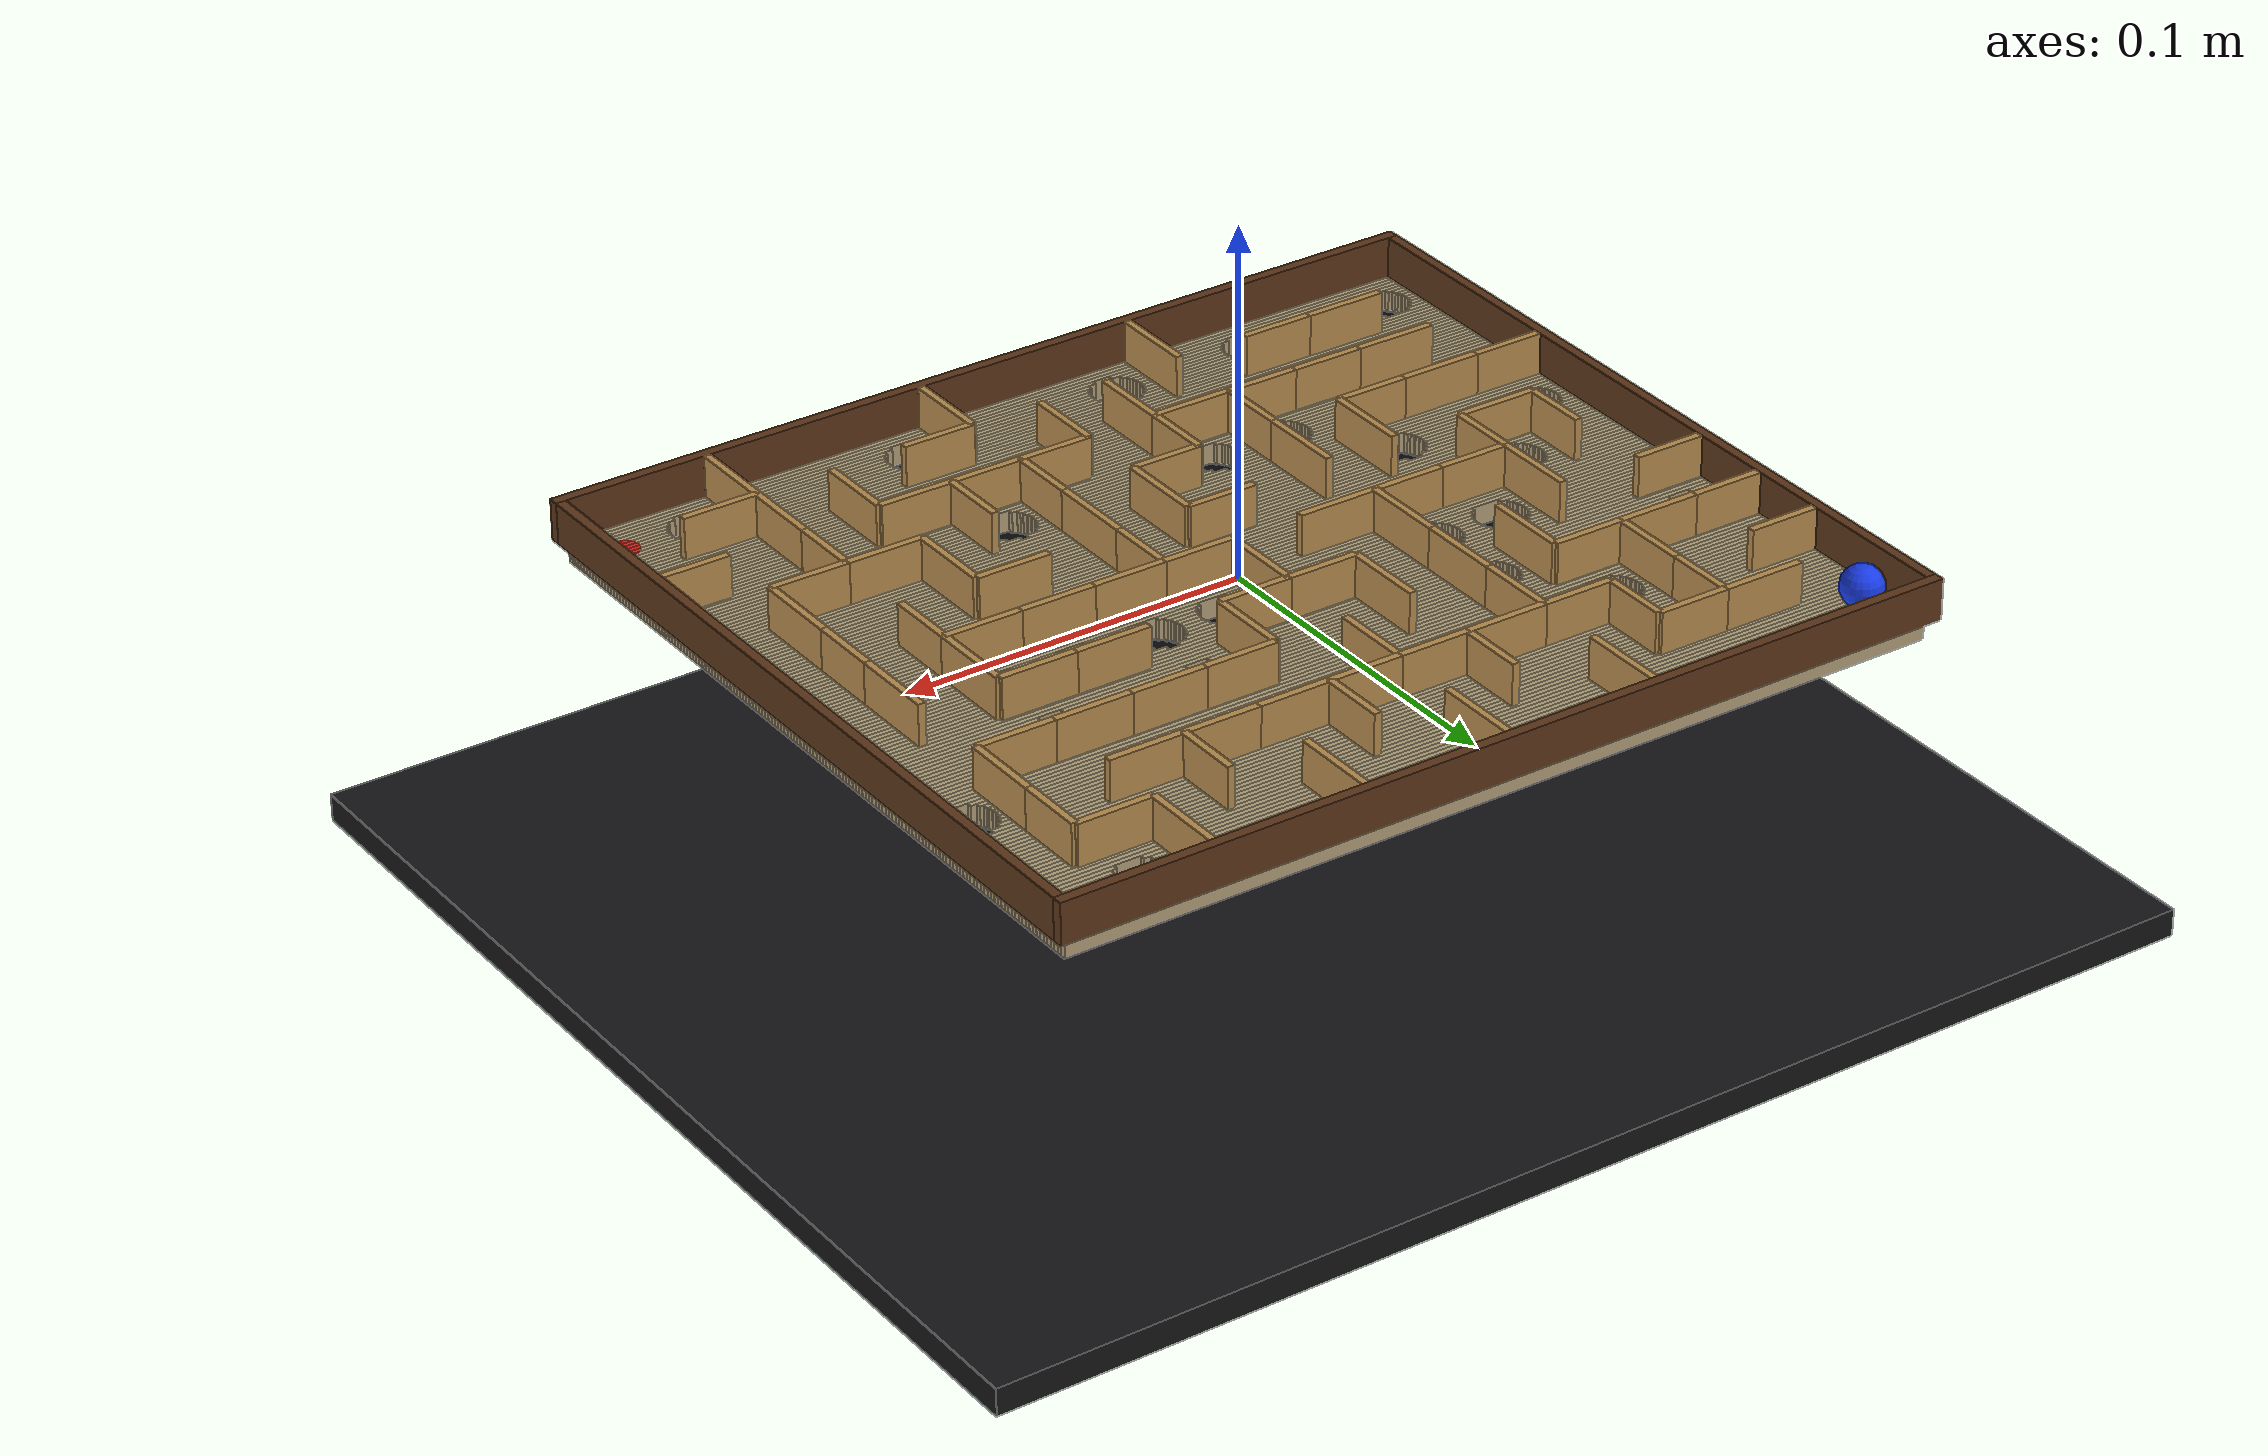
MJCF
<mujoco model="cyberrunner_custom_maze">
  <compiler angle="radian" inertiafromgeom="auto"/>
  <option timestep="0.001" gravity="0 0 -9.81" integrator="implicitfast" solver="Newton" iterations="12" tolerance="1e-9"/>
  <size nconmax="4000" njmax="12000"/>
  <visual>
    <global offwidth="900" offheight="800"/>
    <quality shadowsize="2048"/>
    <map znear="0.01" zfar="3"/>
  </visual>
  <default>
    <default class="floor">
      <geom friction="0.3 0.015 0.002" solref="0.004 1" solimp="0.95 0.99 0.001" density="650"/>
    </default>
    <default class="wall">
      <geom friction="0.35 0.02 0.003" solref="0.003 1" solimp="0.95 0.99 0.001" density="700"/>
    </default>
  </default>
  <worldbody>
    <light name="key" pos="0 -0.15 0.55" dir="0 0 -1" diffuse="0.9 0.9 0.9"/>
    <light name="fill" pos="-0.25 0.2 0.35" dir="0.4 -0.3 -1" diffuse="0.45 0.45 0.45"/>
    <camera name="top" pos="0 0 0.43" quat="1 0 0 0" mode="fixed" fovy="37"/>
    <geom name="catch_tray" type="box" pos="0 0 -0.085" size="0.18 0.16 0.004" rgba="0.08 0.08 0.09 1" friction="0.5 0.02 0.003"/>
    <body name="tilt_x_frame" pos="0 0 0">
      <inertial pos="0 0 0" mass="0.02" diaginertia="0.0001 0.0001 0.0001"/>
      <joint name="tilt_x" type="hinge" axis="1 0 0" range="-0.174532925 0.174532925" damping="0.8" armature="0.01"/>
      <body name="board" pos="0 0 0">
        <joint name="tilt_y" type="hinge" axis="0 1 0" range="-0.174532925 0.174532925" damping="0.8" armature="0.01"/>
        <geom name="floor_0" type="box" pos="0 -0.113751634 -0.003" size="0.1295 0.000748366013 0.003" rgba="0.70 0.63 0.48 1" class="floor"/><geom name="floor_1" type="box" pos="0 -0.112254902 -0.003" size="0.1295 0.000748366013 0.003" rgba="0.70 0.63 0.48 1" class="floor"/><geom name="floor_2" type="box" pos="0 -0.11075817 -0.003" size="0.1295 0.000748366013 0.003" rgba="0.70 0.63 0.48 1" class="floor"/><geom name="floor_3" type="box" pos="-0.125660346 -0.109261438 -0.003" size="0.00383965408 0.000748366013 0.003" rgba="0.70 0.63 0.48 1" class="floor"/><geom name="floor_4" type="box" pos="-0.0969090927 -0.109261438 -0.003" size="0.0195781026 0.000748366013 0.003" rgba="0.70 0.63 0.48 1" class="floor"/><geom name="floor_5" type="box" pos="-0.0531306224 -0.109261438 -0.003" size="0.0188668711 0.000748366013 0.003" rgba="0.70 0.63 0.48 1" class="floor"/><geom name="floor_6" type="box" pos="0.000510589955 -0.109261438 -0.003" size="0.0294408447 0.000748366013 0.003" rgba="0.70 0.63 0.48 1" class="floor"/><geom name="floor_7" type="box" pos="0.0656764118 -0.109261438 -0.003" size="0.0303914806 0.000748366013 0.003" rgba="0.70 0.63 0.48 1" class="floor"/><geom name="floor_8" type="box" pos="0.115450694 -0.109261438 -0.003" size="0.0140493055 0.000748366013 0.003" rgba="0.70 0.63 0.48 1" class="floor"/><geom name="floor_9" type="box" pos="-0.126869371 -0.107764706 -0.003" size="0.0026306292 0.000748366013 0.003" rgba="0.70 0.63 0.48 1" class="floor"/><geom name="floor_10" type="box" pos="-0.0969090927 -0.107764706 -0.003" size="0.0171600529 0.000748366013 0.003" rgba="0.70 0.63 0.48 1" class="floor"/><geom name="floor_11" type="box" pos="-0.0531306224 -0.107764706 -0.003" size="0.0164488213 0.000748366013 0.003" rgba="0.70 0.63 0.48 1" class="floor"/><geom name="floor_12" type="box" pos="0.000510589955 -0.107764706 -0.003" size="0.027022795 0.000748366013 0.003" rgba="0.70 0.63 0.48 1" class="floor"/><geom name="floor_13" type="box" pos="0.0656764118 -0.107764706 -0.003" size="0.0279734308 0.000748366013 0.003" rgba="0.70 0.63 0.48 1" class="floor"/><geom name="floor_14" type="box" pos="0.116659719 -0.107764706 -0.003" size="0.0128402807 0.000748366013 0.003" rgba="0.70 0.63 0.48 1" class="floor"/><geom name="floor_15" type="box" pos="-0.127493925 -0.106267974 -0.003" size="0.00200607454 0.000748366013 0.003" rgba="0.70 0.63 0.48 1" class="floor"/><geom name="floor_16" type="box" pos="-0.0969090927 -0.106267974 -0.003" size="0.0159109436 0.000748366013 0.003" rgba="0.70 0.63 0.48 1" class="floor"/><geom name="floor_17" type="box" pos="-0.0531306224 -0.106267974 -0.003" size="0.015199712 0.000748366013 0.003" rgba="0.70 0.63 0.48 1" class="floor"/><geom name="floor_18" type="box" pos="0.000510589955 -0.106267974 -0.003" size="0.0257736857 0.000748366013 0.003" rgba="0.70 0.63 0.48 1" class="floor"/><geom name="floor_19" type="box" pos="0.0656764118 -0.106267974 -0.003" size="0.0267243215 0.000748366013 0.003" rgba="0.70 0.63 0.48 1" class="floor"/><geom name="floor_20" type="box" pos="0.117284274 -0.106267974 -0.003" size="0.012215726 0.000748366013 0.003" rgba="0.70 0.63 0.48 1" class="floor"/><geom name="floor_21" type="box" pos="-0.12785901 -0.104771242 -0.003" size="0.00164098985 0.000748366013 0.003" rgba="0.70 0.63 0.48 1" class="floor"/><geom name="floor_22" type="box" pos="-0.0969090927 -0.104771242 -0.003" size="0.0151807742 0.000748366013 0.003" rgba="0.70 0.63 0.48 1" class="floor"/><geom name="floor_23" type="box" pos="-0.0531306224 -0.104771242 -0.003" size="0.0144695426 0.000748366013 0.003" rgba="0.70 0.63 0.48 1" class="floor"/><geom name="floor_24" type="box" pos="0.000510589955 -0.104771242 -0.003" size="0.0250435163 0.000748366013 0.003" rgba="0.70 0.63 0.48 1" class="floor"/><geom name="floor_25" type="box" pos="0.0656764118 -0.104771242 -0.003" size="0.0259941521 0.000748366013 0.003" rgba="0.70 0.63 0.48 1" class="floor"/><geom name="floor_26" type="box" pos="0.117649359 -0.104771242 -0.003" size="0.0118506413 0.000748366013 0.003" rgba="0.70 0.63 0.48 1" class="floor"/><geom name="floor_27" type="box" pos="-0.128041927 -0.10327451 -0.003" size="0.00145807316 0.000748366013 0.003" rgba="0.70 0.63 0.48 1" class="floor"/><geom name="floor_28" type="box" pos="-0.0969090927 -0.10327451 -0.003" size="0.0148149408 0.000748366013 0.003" rgba="0.70 0.63 0.48 1" class="floor"/><geom name="floor_29" type="box" pos="-0.0531306224 -0.10327451 -0.003" size="0.0141037093 0.000748366013 0.003" rgba="0.70 0.63 0.48 1" class="floor"/><geom name="floor_30" type="box" pos="0.000510589955 -0.10327451 -0.003" size="0.0246776829 0.000748366013 0.003" rgba="0.70 0.63 0.48 1" class="floor"/><geom name="floor_31" type="box" pos="0.0656764118 -0.10327451 -0.003" size="0.0256283187 0.000748366013 0.003" rgba="0.70 0.63 0.48 1" class="floor"/><geom name="floor_32" type="box" pos="0.117832275 -0.10327451 -0.003" size="0.0116677246 0.000748366013 0.003" rgba="0.70 0.63 0.48 1" class="floor"/><geom name="floor_33" type="box" pos="-0.128069482 -0.101777778 -0.003" size="0.00143051787 0.000748366013 0.003" rgba="0.70 0.63 0.48 1" class="floor"/><geom name="floor_34" type="box" pos="-0.0969090927 -0.101777778 -0.003" size="0.0147598302 0.000748366013 0.003" rgba="0.70 0.63 0.48 1" class="floor"/><geom name="floor_35" type="box" pos="-0.0531306224 -0.101777778 -0.003" size="0.0140485987 0.000748366013 0.003" rgba="0.70 0.63 0.48 1" class="floor"/><geom name="floor_36" type="box" pos="0.000510589955 -0.101777778 -0.003" size="0.0246225723 0.000748366013 0.003" rgba="0.70 0.63 0.48 1" class="floor"/><geom name="floor_37" type="box" pos="0.0656764118 -0.101777778 -0.003" size="0.0255732081 0.000748366013 0.003" rgba="0.70 0.63 0.48 1" class="floor"/><geom name="floor_38" type="box" pos="0.117859831 -0.101777778 -0.003" size="0.0116401693 0.000748366013 0.003" rgba="0.70 0.63 0.48 1" class="floor"/><geom name="floor_39" type="box" pos="-0.127945227 -0.100281046 -0.003" size="0.0015547727 0.000748366013 0.003" rgba="0.70 0.63 0.48 1" class="floor"/><geom name="floor_40" type="box" pos="-0.0969090927 -0.100281046 -0.003" size="0.0150083399 0.000748366013 0.003" rgba="0.70 0.63 0.48 1" class="floor"/><geom name="floor_41" type="box" pos="-0.0531306224 -0.100281046 -0.003" size="0.0142971083 0.000748366013 0.003" rgba="0.70 0.63 0.48 1" class="floor"/><geom name="floor_42" type="box" pos="0.000510589955 -0.100281046 -0.003" size="0.024871082 0.000748366013 0.003" rgba="0.70 0.63 0.48 1" class="floor"/><geom name="floor_43" type="box" pos="0.0656764118 -0.100281046 -0.003" size="0.0258217178 0.000748366013 0.003" rgba="0.70 0.63 0.48 1" class="floor"/><geom name="floor_44" type="box" pos="0.117735576 -0.100281046 -0.003" size="0.0117644242 0.000748366013 0.003" rgba="0.70 0.63 0.48 1" class="floor"/><geom name="floor_45" type="box" pos="-0.127652187 -0.0987843137 -0.003" size="0.0018478126 0.000748366013 0.003" rgba="0.70 0.63 0.48 1" class="floor"/><geom name="floor_46" type="box" pos="-0.0969090927 -0.0987843137 -0.003" size="0.0155944197 0.000748366013 0.003" rgba="0.70 0.63 0.48 1" class="floor"/><geom name="floor_47" type="box" pos="-0.0531306224 -0.0987843137 -0.003" size="0.0148831881 0.000748366013 0.003" rgba="0.70 0.63 0.48 1" class="floor"/><geom name="floor_48" type="box" pos="0.000510589955 -0.0987843137 -0.003" size="0.0254571618 0.000748366013 0.003" rgba="0.70 0.63 0.48 1" class="floor"/><geom name="floor_49" type="box" pos="0.0656764118 -0.0987843137 -0.003" size="0.0264077976 0.000748366013 0.003" rgba="0.70 0.63 0.48 1" class="floor"/><geom name="floor_50" type="box" pos="0.117442536 -0.0987843137 -0.003" size="0.0120574641 0.000748366013 0.003" rgba="0.70 0.63 0.48 1" class="floor"/><geom name="floor_51" type="box" pos="-0.127138064 -0.0972875817 -0.003" size="0.00236193565 0.000748366013 0.003" rgba="0.70 0.63 0.48 1" class="floor"/><geom name="floor_52" type="box" pos="-0.0969090927 -0.0972875817 -0.003" size="0.0166226658 0.000748366013 0.003" rgba="0.70 0.63 0.48 1" class="floor"/><geom name="floor_53" type="box" pos="-0.0531306224 -0.0972875817 -0.003" size="0.0159114342 0.000748366013 0.003" rgba="0.70 0.63 0.48 1" class="floor"/><geom name="floor_54" type="box" pos="0.000510589955 -0.0972875817 -0.003" size="0.0264854079 0.000748366013 0.003" rgba="0.70 0.63 0.48 1" class="floor"/><geom name="floor_55" type="box" pos="0.0656764118 -0.0972875817 -0.003" size="0.0274360437 0.000748366013 0.003" rgba="0.70 0.63 0.48 1" class="floor"/><geom name="floor_56" type="box" pos="0.116928413 -0.0972875817 -0.003" size="0.0125715871 0.000748366013 0.003" rgba="0.70 0.63 0.48 1" class="floor"/><geom name="floor_57" type="box" pos="-0.126231524 -0.0957908497 -0.003" size="0.00326847562 0.000748366013 0.003" rgba="0.70 0.63 0.48 1" class="floor"/><geom name="floor_58" type="box" pos="-0.0969090927 -0.0957908497 -0.003" size="0.0184357457 0.000748366013 0.003" rgba="0.70 0.63 0.48 1" class="floor"/><geom name="floor_59" type="box" pos="-0.0531306224 -0.0957908497 -0.003" size="0.0177245142 0.000748366013 0.003" rgba="0.70 0.63 0.48 1" class="floor"/><geom name="floor_60" type="box" pos="0.000510589955 -0.0957908497 -0.003" size="0.0282984878 0.000748366013 0.003" rgba="0.70 0.63 0.48 1" class="floor"/><geom name="floor_61" type="box" pos="0.0656764118 -0.0957908497 -0.003" size="0.0292491237 0.000748366013 0.003" rgba="0.70 0.63 0.48 1" class="floor"/><geom name="floor_62" type="box" pos="0.116021873 -0.0957908497 -0.003" size="0.0134781271 0.000748366013 0.003" rgba="0.70 0.63 0.48 1" class="floor"/><geom name="floor_63" type="box" pos="0 -0.0942941176 -0.003" size="0.1295 0.000748366013 0.003" rgba="0.70 0.63 0.48 1" class="floor"/><geom name="floor_64" type="box" pos="0 -0.0927973856 -0.003" size="0.1295 0.000748366013 0.003" rgba="0.70 0.63 0.48 1" class="floor"/><geom name="floor_65" type="box" pos="0 -0.0913006536 -0.003" size="0.1295 0.000748366013 0.003" rgba="0.70 0.63 0.48 1" class="floor"/><geom name="floor_66" type="box" pos="0 -0.0898039216 -0.003" size="0.1295 0.000748366013 0.003" rgba="0.70 0.63 0.48 1" class="floor"/><geom name="floor_67" type="box" pos="0 -0.0883071895 -0.003" size="0.1295 0.000748366013 0.003" rgba="0.70 0.63 0.48 1" class="floor"/><geom name="floor_68" type="box" pos="0 -0.0868104575 -0.003" size="0.1295 0.000748366013 0.003" rgba="0.70 0.63 0.48 1" class="floor"/><geom name="floor_69" type="box" pos="0 -0.0853137255 -0.003" size="0.1295 0.000748366013 0.003" rgba="0.70 0.63 0.48 1" class="floor"/><geom name="floor_70" type="box" pos="0 -0.0838169935 -0.003" size="0.1295 0.000748366013 0.003" rgba="0.70 0.63 0.48 1" class="floor"/><geom name="floor_71" type="box" pos="0 -0.0823202614 -0.003" size="0.1295 0.000748366013 0.003" rgba="0.70 0.63 0.48 1" class="floor"/><geom name="floor_72" type="box" pos="0 -0.0808235294 -0.003" size="0.1295 0.000748366013 0.003" rgba="0.70 0.63 0.48 1" class="floor"/><geom name="floor_73" type="box" pos="0 -0.0793267974 -0.003" size="0.1295 0.000748366013 0.003" rgba="0.70 0.63 0.48 1" class="floor"/><geom name="floor_74" type="box" pos="0 -0.0778300654 -0.003" size="0.1295 0.000748366013 0.003" rgba="0.70 0.63 0.48 1" class="floor"/><geom name="floor_75" type="box" pos="0 -0.0763333333 -0.003" size="0.1295 0.000748366013 0.003" rgba="0.70 0.63 0.48 1" class="floor"/><geom name="floor_76" type="box" pos="0 -0.0748366013 -0.003" size="0.1295 0.000748366013 0.003" rgba="0.70 0.63 0.48 1" class="floor"/><geom name="floor_77" type="box" pos="0 -0.0733398693 -0.003" size="0.1295 0.000748366013 0.003" rgba="0.70 0.63 0.48 1" class="floor"/><geom name="floor_78" type="box" pos="0 -0.0718431373 -0.003" size="0.1295 0.000748366013 0.003" rgba="0.70 0.63 0.48 1" class="floor"/><geom name="floor_79" type="box" pos="0 -0.0703464052 -0.003" size="0.1295 0.000748366013 0.003" rgba="0.70 0.63 0.48 1" class="floor"/><geom name="floor_80" type="box" pos="0 -0.0688496732 -0.003" size="0.1295 0.000748366013 0.003" rgba="0.70 0.63 0.48 1" class="floor"/><geom name="floor_81" type="box" pos="0 -0.0673529412 -0.003" size="0.1295 0.000748366013 0.003" rgba="0.70 0.63 0.48 1" class="floor"/><geom name="floor_82" type="box" pos="0 -0.0658562092 -0.003" size="0.1295 0.000748366013 0.003" rgba="0.70 0.63 0.48 1" class="floor"/><geom name="floor_83" type="box" pos="0 -0.0643594771 -0.003" size="0.1295 0.000748366013 0.003" rgba="0.70 0.63 0.48 1" class="floor"/><geom name="floor_84" type="box" pos="-0.115454923 -0.0628627451 -0.003" size="0.0140450772 0.000748366013 0.003" rgba="0.70 0.63 0.48 1" class="floor"/><geom name="floor_85" type="box" pos="-0.0753875232 -0.0628627451 -0.003" size="0.017136711 0.000748366013 0.003" rgba="0.70 0.63 0.48 1" class="floor"/><geom name="floor_86" type="box" pos="-0.0427025048 -0.0628627451 -0.003" size="0.00666269609 0.000748366013 0.003" rgba="0.70 0.63 0.48 1" class="floor"/><geom name="floor_87" type="box" pos="0.000510589955 -0.0628627451 -0.003" size="0.0276647873 0.000748366013 0.003" rgba="0.70 0.63 0.48 1" class="floor"/><geom name="floor_88" type="box" pos="0.0832804943 -0.0628627451 -0.003" size="0.0462195057 0.000748366013 0.003" rgba="0.70 0.63 0.48 1" class="floor"/><geom name="floor_89" type="box" pos="-0.11621623 -0.0613660131 -0.003" size="0.0132837699 0.000748366013 0.003" rgba="0.70 0.63 0.48 1" class="floor"/><geom name="floor_90" type="box" pos="-0.0753875232 -0.0613660131 -0.003" size="0.0156140962 0.000748366013 0.003" rgba="0.70 0.63 0.48 1" class="floor"/><geom name="floor_91" type="box" pos="-0.0427025048 -0.0613660131 -0.003" size="0.00514008135 0.000748366013 0.003" rgba="0.70 0.63 0.48 1" class="floor"/><geom name="floor_92" type="box" pos="0.000510589955 -0.0613660131 -0.003" size="0.0261421726 0.000748366013 0.003" rgba="0.70 0.63 0.48 1" class="floor"/><geom name="floor_93" type="box" pos="0.0840418017 -0.0613660131 -0.003" size="0.0454581983 0.000748366013 0.003" rgba="0.70 0.63 0.48 1" class="floor"/><geom name="floor_94" type="box" pos="-0.116659653 -0.059869281 -0.003" size="0.0128403472 0.000748366013 0.003" rgba="0.70 0.63 0.48 1" class="floor"/><geom name="floor_95" type="box" pos="-0.0753875232 -0.059869281 -0.003" size="0.0147272509 0.000748366013 0.003" rgba="0.70 0.63 0.48 1" class="floor"/><geom name="floor_96" type="box" pos="-0.0427025048 -0.059869281 -0.003" size="0.00425323604 0.000748366013 0.003" rgba="0.70 0.63 0.48 1" class="floor"/><geom name="floor_97" type="box" pos="0.000510589955 -0.059869281 -0.003" size="0.0252553273 0.000748366013 0.003" rgba="0.70 0.63 0.48 1" class="floor"/><geom name="floor_98" type="box" pos="0.0844852243 -0.059869281 -0.003" size="0.0450147757 0.000748366013 0.003" rgba="0.70 0.63 0.48 1" class="floor"/><geom name="floor_99" type="box" pos="-0.116902322 -0.058372549 -0.003" size="0.0125976779 0.000748366013 0.003" rgba="0.70 0.63 0.48 1" class="floor"/><geom name="floor_100" type="box" pos="-0.0753875232 -0.058372549 -0.003" size="0.0142419123 0.000748366013 0.003" rgba="0.70 0.63 0.48 1" class="floor"/><geom name="floor_101" type="box" pos="-0.0427025048 -0.058372549 -0.003" size="0.00376789746 0.000748366013 0.003" rgba="0.70 0.63 0.48 1" class="floor"/><geom name="floor_102" type="box" pos="0.000510589955 -0.058372549 -0.003" size="0.0247699887 0.000748366013 0.003" rgba="0.70 0.63 0.48 1" class="floor"/><geom name="floor_103" type="box" pos="0.0847278936 -0.058372549 -0.003" size="0.0447721064 0.000748366013 0.003" rgba="0.70 0.63 0.48 1" class="floor"/><geom name="floor_104" type="box" pos="-0.116983417 -0.056875817 -0.003" size="0.0125165829 0.000748366013 0.003" rgba="0.70 0.63 0.48 1" class="floor"/><geom name="floor_105" type="box" pos="-0.0753875232 -0.056875817 -0.003" size="0.0140797223 0.000748366013 0.003" rgba="0.70 0.63 0.48 1" class="floor"/><geom name="floor_106" type="box" pos="-0.0427025048 -0.056875817 -0.003" size="0.00360570744 0.000748366013 0.003" rgba="0.70 0.63 0.48 1" class="floor"/><geom name="floor_107" type="box" pos="0.000510589955 -0.056875817 -0.003" size="0.0246077987 0.000748366013 0.003" rgba="0.70 0.63 0.48 1" class="floor"/><geom name="floor_108" type="box" pos="0.0848089886 -0.056875817 -0.003" size="0.0446910114 0.000748366013 0.003" rgba="0.70 0.63 0.48 1" class="floor"/><geom name="floor_109" type="box" pos="-0.116913635 -0.055379085 -0.003" size="0.0125863653 0.000748366013 0.003" rgba="0.70 0.63 0.48 1" class="floor"/><geom name="floor_110" type="box" pos="-0.0753875232 -0.055379085 -0.003" size="0.0142192871 0.000748366013 0.003" rgba="0.70 0.63 0.48 1" class="floor"/><geom name="floor_111" type="box" pos="-0.0427025048 -0.055379085 -0.003" size="0.0037452722 0.000748366013 0.003" rgba="0.70 0.63 0.48 1" class="floor"/><geom name="floor_112" type="box" pos="0.000510589955 -0.055379085 -0.003" size="0.0247473634 0.000748366013 0.003" rgba="0.70 0.63 0.48 1" class="floor"/><geom name="floor_113" type="box" pos="0.0847392063 -0.055379085 -0.003" size="0.0447607937 0.000748366013 0.003" rgba="0.70 0.63 0.48 1" class="floor"/><geom name="floor_114" type="box" pos="-0.116683833 -0.0538823529 -0.003" size="0.0128161674 0.000748366013 0.003" rgba="0.70 0.63 0.48 1" class="floor"/><geom name="floor_115" type="box" pos="-0.0753875232 -0.0538823529 -0.003" size="0.0146788913 0.000748366013 0.003" rgba="0.70 0.63 0.48 1" class="floor"/><geom name="floor_116" type="box" pos="-0.0427025048 -0.0538823529 -0.003" size="0.00420487643 0.000748366013 0.003" rgba="0.70 0.63 0.48 1" class="floor"/><geom name="floor_117" type="box" pos="0.000510589955 -0.0538823529 -0.003" size="0.0252069677 0.000748366013 0.003" rgba="0.70 0.63 0.48 1" class="floor"/><geom name="floor_118" type="box" pos="0.0845094041 -0.0538823529 -0.003" size="0.0449905959 0.000748366013 0.003" rgba="0.70 0.63 0.48 1" class="floor"/><geom name="floor_119" type="box" pos="-0.11625775 -0.0523856209 -0.003" size="0.0132422501 0.000748366013 0.003" rgba="0.70 0.63 0.48 1" class="floor"/><geom name="floor_120" type="box" pos="-0.0753875232 -0.0523856209 -0.003" size="0.0155310567 0.000748366013 0.003" rgba="0.70 0.63 0.48 1" class="floor"/><geom name="floor_121" type="box" pos="-0.0427025048 -0.0523856209 -0.003" size="0.00505704185 0.000748366013 0.003" rgba="0.70 0.63 0.48 1" class="floor"/><geom name="floor_122" type="box" pos="0.000510589955 -0.0523856209 -0.003" size="0.0260591331 0.000748366013 0.003" rgba="0.70 0.63 0.48 1" class="floor"/><geom name="floor_123" type="box" pos="0.0840833214 -0.0523856209 -0.003" size="0.0454166786 0.000748366013 0.003" rgba="0.70 0.63 0.48 1" class="floor"/><geom name="floor_124" type="box" pos="-0.115528552 -0.0508888889 -0.003" size="0.0139714479 0.000748366013 0.003" rgba="0.70 0.63 0.48 1" class="floor"/><geom name="floor_125" type="box" pos="-0.0753875232 -0.0508888889 -0.003" size="0.0169894522 0.000748366013 0.003" rgba="0.70 0.63 0.48 1" class="floor"/><geom name="floor_126" type="box" pos="-0.0427025048 -0.0508888889 -0.003" size="0.00651543738 0.000748366013 0.003" rgba="0.70 0.63 0.48 1" class="floor"/><geom name="floor_127" type="box" pos="0.000510589955 -0.0508888889 -0.003" size="0.0275175286 0.000748366013 0.003" rgba="0.70 0.63 0.48 1" class="floor"/><geom name="floor_128" type="box" pos="0.0833541237 -0.0508888889 -0.003" size="0.0461458763 0.000748366013 0.003" rgba="0.70 0.63 0.48 1" class="floor"/><geom name="floor_129" type="box" pos="-0.113751473 -0.0493921569 -0.003" size="0.0157485271 0.000748366013 0.003" rgba="0.70 0.63 0.48 1" class="floor"/><geom name="floor_130" type="box" pos="-0.0753875232 -0.0493921569 -0.003" size="0.0205436106 0.000748366013 0.003" rgba="0.70 0.63 0.48 1" class="floor"/><geom name="floor_131" type="box" pos="-0.0427025048 -0.0493921569 -0.003" size="0.0100695957 0.000748366013 0.003" rgba="0.70 0.63 0.48 1" class="floor"/><geom name="floor_132" type="box" pos="0.000510589955 -0.0493921569 -0.003" size="0.031071687 0.000748366013 0.003" rgba="0.70 0.63 0.48 1" class="floor"/><geom name="floor_133" type="box" pos="0.0815770445 -0.0493921569 -0.003" size="0.0479229555 0.000748366013 0.003" rgba="0.70 0.63 0.48 1" class="floor"/><geom name="floor_134" type="box" pos="0 -0.0478954248 -0.003" size="0.1295 0.000748366013 0.003" rgba="0.70 0.63 0.48 1" class="floor"/><geom name="floor_135" type="box" pos="0 -0.0463986928 -0.003" size="0.1295 0.000748366013 0.003" rgba="0.70 0.63 0.48 1" class="floor"/><geom name="floor_136" type="box" pos="0 -0.0449019608 -0.003" size="0.1295 0.000748366013 0.003" rgba="0.70 0.63 0.48 1" class="floor"/><geom name="floor_137" type="box" pos="0 -0.0434052288 -0.003" size="0.1295 0.000748366013 0.003" rgba="0.70 0.63 0.48 1" class="floor"/><geom name="floor_138" type="box" pos="0 -0.0419084967 -0.003" size="0.1295 0.000748366013 0.003" rgba="0.70 0.63 0.48 1" class="floor"/><geom name="floor_139" type="box" pos="-0.126379242 -0.0404117647 -0.003" size="0.00312075768 0.000748366013 0.003" rgba="0.70 0.63 0.48 1" class="floor"/><geom name="floor_140" type="box" pos="-0.0969090927 -0.0404117647 -0.003" size="0.0181403098 0.000748366013 0.003" rgba="0.70 0.63 0.48 1" class="floor"/><geom name="floor_141" type="box" pos="-0.0420506256 -0.0404117647 -0.003" size="0.0285090751 0.000748366013 0.003" rgba="0.70 0.63 0.48 1" class="floor"/><geom name="floor_142" type="box" pos="0.0620837659 -0.0404117647 -0.003" size="0.0674162341 0.000748366013 0.003" rgba="0.70 0.63 0.48 1" class="floor"/><geom name="floor_143" type="box" pos="-0.1272165 -0.0389150327 -0.003" size="0.00228349951 0.000748366013 0.003" rgba="0.70 0.63 0.48 1" class="floor"/><geom name="floor_144" type="box" pos="-0.0969090927 -0.0389150327 -0.003" size="0.0164657935 0.000748366013 0.003" rgba="0.70 0.63 0.48 1" class="floor"/><geom name="floor_145" type="box" pos="-0.0420506256 -0.0389150327 -0.003" size="0.0268345588 0.000748366013 0.003" rgba="0.70 0.63 0.48 1" class="floor"/><geom name="floor_146" type="box" pos="0.062921024 -0.0389150327 -0.003" size="0.066578976 0.000748366013 0.003" rgba="0.70 0.63 0.48 1" class="floor"/><geom name="floor_147" type="box" pos="-0.127698445 -0.0374183007 -0.003" size="0.00180155456 0.000748366013 0.003" rgba="0.70 0.63 0.48 1" class="floor"/><geom name="floor_148" type="box" pos="-0.0969090927 -0.0374183007 -0.003" size="0.0155019036 0.000748366013 0.003" rgba="0.70 0.63 0.48 1" class="floor"/><geom name="floor_149" type="box" pos="-0.0420506256 -0.0374183007 -0.003" size="0.0258706689 0.000748366013 0.003" rgba="0.70 0.63 0.48 1" class="floor"/><geom name="floor_150" type="box" pos="0.063402969 -0.0374183007 -0.003" size="0.066097031 0.000748366013 0.003" rgba="0.70 0.63 0.48 1" class="floor"/><geom name="floor_151" type="box" pos="-0.127968975 -0.0359215686 -0.003" size="0.0015310247 0.000748366013 0.003" rgba="0.70 0.63 0.48 1" class="floor"/><geom name="floor_152" type="box" pos="-0.0969090927 -0.0359215686 -0.003" size="0.0149608439 0.000748366013 0.003" rgba="0.70 0.63 0.48 1" class="floor"/><geom name="floor_153" type="box" pos="-0.0420506256 -0.0359215686 -0.003" size="0.0253296092 0.000748366013 0.003" rgba="0.70 0.63 0.48 1" class="floor"/><geom name="floor_154" type="box" pos="0.0636734988 -0.0359215686 -0.003" size="0.0658265012 0.000748366013 0.003" rgba="0.70 0.63 0.48 1" class="floor"/><geom name="floor_155" type="box" pos="-0.128074163 -0.0344248366 -0.003" size="0.00142583709 0.000748366013 0.003" rgba="0.70 0.63 0.48 1" class="floor"/><geom name="floor_156" type="box" pos="-0.0969090927 -0.0344248366 -0.003" size="0.0147504687 0.000748366013 0.003" rgba="0.70 0.63 0.48 1" class="floor"/><geom name="floor_157" type="box" pos="-0.0420506256 -0.0344248366 -0.003" size="0.025119234 0.000748366013 0.003" rgba="0.70 0.63 0.48 1" class="floor"/><geom name="floor_158" type="box" pos="0.0637786864 -0.0344248366 -0.003" size="0.0657213136 0.000748366013 0.003" rgba="0.70 0.63 0.48 1" class="floor"/><geom name="floor_159" type="box" pos="-0.128028132 -0.0329281046 -0.003" size="0.00147186764 0.000748366013 0.003" rgba="0.70 0.63 0.48 1" class="floor"/><geom name="floor_160" type="box" pos="-0.0969090927 -0.0329281046 -0.003" size="0.0148425298 0.000748366013 0.003" rgba="0.70 0.63 0.48 1" class="floor"/><geom name="floor_161" type="box" pos="-0.0420506256 -0.0329281046 -0.003" size="0.0252112951 0.000748366013 0.003" rgba="0.70 0.63 0.48 1" class="floor"/><geom name="floor_162" type="box" pos="0.0637326559 -0.0329281046 -0.003" size="0.0657673441 0.000748366013 0.003" rgba="0.70 0.63 0.48 1" class="floor"/><geom name="floor_163" type="box" pos="-0.127824919 -0.0314313725 -0.003" size="0.00167508103 0.000748366013 0.003" rgba="0.70 0.63 0.48 1" class="floor"/><geom name="floor_164" type="box" pos="-0.0969090927 -0.0314313725 -0.003" size="0.0152489565 0.000748366013 0.003" rgba="0.70 0.63 0.48 1" class="floor"/><geom name="floor_165" type="box" pos="-0.0420506256 -0.0314313725 -0.003" size="0.0256177218 0.000748366013 0.003" rgba="0.70 0.63 0.48 1" class="floor"/><geom name="floor_166" type="box" pos="0.0635294425 -0.0314313725 -0.003" size="0.0659705575 0.000748366013 0.003" rgba="0.70 0.63 0.48 1" class="floor"/><geom name="floor_167" type="box" pos="-0.127433831 -0.0299346405 -0.003" size="0.0020661687 0.000748366013 0.003" rgba="0.70 0.63 0.48 1" class="floor"/><geom name="floor_168" type="box" pos="-0.0969090927 -0.0299346405 -0.003" size="0.0160311319 0.000748366013 0.003" rgba="0.70 0.63 0.48 1" class="floor"/><geom name="floor_169" type="box" pos="-0.0420506256 -0.0299346405 -0.003" size="0.0263998972 0.000748366013 0.003" rgba="0.70 0.63 0.48 1" class="floor"/><geom name="floor_170" type="box" pos="0.0631383548 -0.0299346405 -0.003" size="0.0663616452 0.000748366013 0.003" rgba="0.70 0.63 0.48 1" class="floor"/><geom name="floor_171" type="box" pos="-0.126766114 -0.0284379085 -0.003" size="0.00273388611 0.000748366013 0.003" rgba="0.70 0.63 0.48 1" class="floor"/><geom name="floor_172" type="box" pos="-0.0969090927 -0.0284379085 -0.003" size="0.0173665667 0.000748366013 0.003" rgba="0.70 0.63 0.48 1" class="floor"/><geom name="floor_173" type="box" pos="-0.0420506256 -0.0284379085 -0.003" size="0.027735332 0.000748366013 0.003" rgba="0.70 0.63 0.48 1" class="floor"/><geom name="floor_174" type="box" pos="0.0624706374 -0.0284379085 -0.003" size="0.0670293626 0.000748366013 0.003" rgba="0.70 0.63 0.48 1" class="floor"/><geom name="floor_175" type="box" pos="-0.125388173 -0.0269411765 -0.003" size="0.00411182655 0.000748366013 0.003" rgba="0.70 0.63 0.48 1" class="floor"/><geom name="floor_176" type="box" pos="-0.0969090927 -0.0269411765 -0.003" size="0.0201224476 0.000748366013 0.003" rgba="0.70 0.63 0.48 1" class="floor"/><geom name="floor_177" type="box" pos="-0.0420506256 -0.0269411765 -0.003" size="0.0304912129 0.000748366013 0.003" rgba="0.70 0.63 0.48 1" class="floor"/><geom name="floor_178" type="box" pos="0.061092697 -0.0269411765 -0.003" size="0.068407303 0.000748366013 0.003" rgba="0.70 0.63 0.48 1" class="floor"/><geom name="floor_179" type="box" pos="0 -0.0254444444 -0.003" size="0.1295 0.000748366013 0.003" rgba="0.70 0.63 0.48 1" class="floor"/><geom name="floor_180" type="box" pos="0 -0.0239477124 -0.003" size="0.1295 0.000748366013 0.003" rgba="0.70 0.63 0.48 1" class="floor"/><geom name="floor_181" type="box" pos="0 -0.0224509804 -0.003" size="0.1295 0.000748366013 0.003" rgba="0.70 0.63 0.48 1" class="floor"/><geom name="floor_182" type="box" pos="0 -0.0209542484 -0.003" size="0.1295 0.000748366013 0.003" rgba="0.70 0.63 0.48 1" class="floor"/><geom name="floor_183" type="box" pos="0 -0.0194575163 -0.003" size="0.1295 0.000748366013 0.003" rgba="0.70 0.63 0.48 1" class="floor"/><geom name="floor_184" type="box" pos="-0.115251934 -0.0179607843 -0.003" size="0.0142480656 0.000748366013 0.003" rgba="0.70 0.63 0.48 1" class="floor"/><geom name="floor_185" type="box" pos="-0.0753875232 -0.0179607843 -0.003" size="0.0175426877 0.000748366013 0.003" rgba="0.70 0.63 0.48 1" class="floor"/><geom name="floor_186" type="box" pos="0.0398644112 -0.0179607843 -0.003" size="0.0896355888 0.000748366013 0.003" rgba="0.70 0.63 0.48 1" class="floor"/><geom name="floor_187" type="box" pos="-0.11610481 -0.0164640523 -0.003" size="0.0133951901 0.000748366013 0.003" rgba="0.70 0.63 0.48 1" class="floor"/><geom name="floor_188" type="box" pos="-0.0753875232 -0.0164640523 -0.003" size="0.0158369367 0.000748366013 0.003" rgba="0.70 0.63 0.48 1" class="floor"/><geom name="floor_189" type="box" pos="0.0407172867 -0.0164640523 -0.003" size="0.0887827133 0.000748366013 0.003" rgba="0.70 0.63 0.48 1" class="floor"/><geom name="floor_190" type="box" pos="-0.116594251 -0.0149673203 -0.003" size="0.0129057493 0.000748366013 0.003" rgba="0.70 0.63 0.48 1" class="floor"/><geom name="floor_191" type="box" pos="-0.0753875232 -0.0149673203 -0.003" size="0.014858055 0.000748366013 0.003" rgba="0.70 0.63 0.48 1" class="floor"/><geom name="floor_192" type="box" pos="0.0412067275 -0.0149673203 -0.003" size="0.0882932725 0.000748366013 0.003" rgba="0.70 0.63 0.48 1" class="floor"/><geom name="floor_193" type="box" pos="-0.116870086 -0.0134705882 -0.003" size="0.0126299139 0.000748366013 0.003" rgba="0.70 0.63 0.48 1" class="floor"/><geom name="floor_194" type="box" pos="-0.0753875232 -0.0134705882 -0.003" size="0.0143063842 0.000748366013 0.003" rgba="0.70 0.63 0.48 1" class="floor"/><geom name="floor_195" type="box" pos="0.0414825629 -0.0134705882 -0.003" size="0.0880174371 0.000748366013 0.003" rgba="0.70 0.63 0.48 1" class="floor"/><geom name="floor_196" type="box" pos="-0.1169798 -0.0119738562 -0.003" size="0.0125202003 0.000748366013 0.003" rgba="0.70 0.63 0.48 1" class="floor"/><geom name="floor_197" type="box" pos="-0.0753875232 -0.0119738562 -0.003" size="0.014086957 0.000748366013 0.003" rgba="0.70 0.63 0.48 1" class="floor"/><geom name="floor_198" type="box" pos="0.0415922765 -0.0119738562 -0.003" size="0.0879077235 0.000748366013 0.003" rgba="0.70 0.63 0.48 1" class="floor"/><geom name="floor_199" type="box" pos="-0.11693818 -0.0104771242 -0.003" size="0.0125618198 0.000748366013 0.003" rgba="0.70 0.63 0.48 1" class="floor"/><geom name="floor_200" type="box" pos="-0.0753875232 -0.0104771242 -0.003" size="0.014170196 0.000748366013 0.003" rgba="0.70 0.63 0.48 1" class="floor"/><geom name="floor_201" type="box" pos="0.041550657 -0.0104771242 -0.003" size="0.087949343 0.000748366013 0.003" rgba="0.70 0.63 0.48 1" class="floor"/><geom name="floor_202" type="box" pos="-0.116739843 -0.00898039216 -0.003" size="0.0127601572 0.000748366013 0.003" rgba="0.70 0.63 0.48 1" class="floor"/><geom name="floor_203" type="box" pos="-0.0753875232 -0.00898039216 -0.003" size="0.0145668709 0.000748366013 0.003" rgba="0.70 0.63 0.48 1" class="floor"/><geom name="floor_204" type="box" pos="0.0413523196 -0.00898039216 -0.003" size="0.0881476804 0.000748366013 0.003" rgba="0.70 0.63 0.48 1" class="floor"/><geom name="floor_205" type="box" pos="-0.116355056 -0.00748366013 -0.003" size="0.0131449438 0.000748366013 0.003" rgba="0.70 0.63 0.48 1" class="floor"/><geom name="floor_206" type="box" pos="-0.0753875232 -0.00748366013 -0.003" size="0.015336444 0.000748366013 0.003" rgba="0.70 0.63 0.48 1" class="floor"/><geom name="floor_207" type="box" pos="0.040967533 -0.00748366013 -0.003" size="0.088532467 0.000748366013 0.003" rgba="0.70 0.63 0.48 1" class="floor"/><geom name="floor_208" type="box" pos="-0.115697982 -0.0059869281 -0.003" size="0.0138020178 0.000748366013 0.003" rgba="0.70 0.63 0.48 1" class="floor"/><geom name="floor_209" type="box" pos="-0.0753875232 -0.0059869281 -0.003" size="0.0166505921 0.000748366013 0.003" rgba="0.70 0.63 0.48 1" class="floor"/><geom name="floor_210" type="box" pos="0.040310459 -0.0059869281 -0.003" size="0.089189541 0.000748366013 0.003" rgba="0.70 0.63 0.48 1" class="floor"/><geom name="floor_211" type="box" pos="-0.114366241 -0.00449019608 -0.003" size="0.0151337594 0.000748366013 0.003" rgba="0.70 0.63 0.48 1" class="floor"/><geom name="floor_212" type="box" pos="-0.0753875232 -0.00449019608 -0.003" size="0.0193140753 0.000748366013 0.003" rgba="0.70 0.63 0.48 1" class="floor"/><geom name="floor_213" type="box" pos="0.0389787174 -0.00449019608 -0.003" size="0.0905212826 0.000748366013 0.003" rgba="0.70 0.63 0.48 1" class="floor"/><geom name="floor_214" type="box" pos="0 -0.00299346405 -0.003" size="0.1295 0.000748366013 0.003" rgba="0.70 0.63 0.48 1" class="floor"/><geom name="floor_215" type="box" pos="0 -0.00149673203 -0.003" size="0.1295 0.000748366013 0.003" rgba="0.70 0.63 0.48 1" class="floor"/><geom name="floor_216" type="box" pos="0 -1.38777878e-17 -0.003" size="0.1295 0.000748366013 0.003" rgba="0.70 0.63 0.48 1" class="floor"/><geom name="floor_217" type="box" pos="0 0.00149673203 -0.003" size="0.1295 0.000748366013 0.003" rgba="0.70 0.63 0.48 1" class="floor"/><geom name="floor_218" type="box" pos="0 0.00299346405 -0.003" size="0.1295 0.000748366013 0.003" rgba="0.70 0.63 0.48 1" class="floor"/><geom name="floor_219" type="box" pos="-0.104212336 0.00449019608 -0.003" size="0.0252876635 0.000748366013 0.003" rgba="0.70 0.63 0.48 1" class="floor"/><geom name="floor_220" type="box" pos="-0.0642361242 0.00449019608 -0.003" size="0.00616768636 0.000748366013 0.003" rgba="0.70 0.63 0.48 1" class="floor"/><geom name="floor_221" type="box" pos="-0.0211880621 0.00449019608 -0.003" size="0.0283595132 0.000748366013 0.003" rgba="0.70 0.63 0.48 1" class="floor"/><geom name="floor_222" type="box" pos="0.0220250326 0.00449019608 -0.003" size="0.00633271909 0.000748366013 0.003" rgba="0.70 0.63 0.48 1" class="floor"/><geom name="floor_223" type="box" pos="0.0434108554 0.00449019608 -0.003" size="0.0065322412 0.000748366013 0.003" rgba="0.70 0.63 0.48 1" class="floor"/><geom name="floor_224" type="box" pos="0.0652626054 0.00449019608 -0.003" size="0.00679864632 0.000748366013 0.003" rgba="0.70 0.63 0.48 1" class="floor"/><geom name="floor_225" type="box" pos="0.105041057 0.00449019608 -0.003" size="0.0244589429 0.000748366013 0.003" rgba="0.70 0.63 0.48 1" class="floor"/><geom name="floor_226" type="box" pos="-0.105014184 0.0059869281 -0.003" size="0.0244858161 0.000748366013 0.003" rgba="0.70 0.63 0.48 1" class="floor"/><geom name="floor_227" type="box" pos="-0.0642361242 0.0059869281 -0.003" size="0.00456399153 0.000748366013 0.003" rgba="0.70 0.63 0.48 1" class="floor"/><geom name="floor_228" type="box" pos="-0.0211880621 0.0059869281 -0.003" size="0.0267558184 0.000748366013 0.003" rgba="0.70 0.63 0.48 1" class="floor"/><geom name="floor_229" type="box" pos="0.0220250326 0.0059869281 -0.003" size="0.00472902426 0.000748366013 0.003" rgba="0.70 0.63 0.48 1" class="floor"/><geom name="floor_230" type="box" pos="0.0434108554 0.0059869281 -0.003" size="0.00492854637 0.000748366013 0.003" rgba="0.70 0.63 0.48 1" class="floor"/><geom name="floor_231" type="box" pos="0.0652626054 0.0059869281 -0.003" size="0.00519495149 0.000748366013 0.003" rgba="0.70 0.63 0.48 1" class="floor"/><geom name="floor_232" type="box" pos="0.105842905 0.0059869281 -0.003" size="0.0236570955 0.000748366013 0.003" rgba="0.70 0.63 0.48 1" class="floor"/><geom name="floor_233" type="box" pos="-0.105478599 0.00748366013 -0.003" size="0.0240214008 0.000748366013 0.003" rgba="0.70 0.63 0.48 1" class="floor"/><geom name="floor_234" type="box" pos="-0.0642361242 0.00748366013 -0.003" size="0.00363516086 0.000748366013 0.003" rgba="0.70 0.63 0.48 1" class="floor"/><geom name="floor_235" type="box" pos="-0.0211880621 0.00748366013 -0.003" size="0.0258269877 0.000748366013 0.003" rgba="0.70 0.63 0.48 1" class="floor"/><geom name="floor_236" type="box" pos="0.0220250326 0.00748366013 -0.003" size="0.00380019359 0.000748366013 0.003" rgba="0.70 0.63 0.48 1" class="floor"/><geom name="floor_237" type="box" pos="0.0434108554 0.00748366013 -0.003" size="0.0039997157 0.000748366013 0.003" rgba="0.70 0.63 0.48 1" class="floor"/><geom name="floor_238" type="box" pos="0.0652626054 0.00748366013 -0.003" size="0.00426612082 0.000748366013 0.003" rgba="0.70 0.63 0.48 1" class="floor"/><geom name="floor_239" type="box" pos="0.10630732 0.00748366013 -0.003" size="0.0231926802 0.000748366013 0.003" rgba="0.70 0.63 0.48 1" class="floor"/><geom name="floor_240" type="box" pos="-0.105736575 0.00898039216 -0.003" size="0.0237634252 0.000748366013 0.003" rgba="0.70 0.63 0.48 1" class="floor"/><geom name="floor_241" type="box" pos="-0.0642361242 0.00898039216 -0.003" size="0.00311920972 0.000748366013 0.003" rgba="0.70 0.63 0.48 1" class="floor"/><geom name="floor_242" type="box" pos="-0.0211880621 0.00898039216 -0.003" size="0.0253110366 0.000748366013 0.003" rgba="0.70 0.63 0.48 1" class="floor"/><geom name="floor_243" type="box" pos="0.0220250326 0.00898039216 -0.003" size="0.00328424244 0.000748366013 0.003" rgba="0.70 0.63 0.48 1" class="floor"/><geom name="floor_244" type="box" pos="0.0434108554 0.00898039216 -0.003" size="0.00348376456 0.000748366013 0.003" rgba="0.70 0.63 0.48 1" class="floor"/><geom name="floor_245" type="box" pos="0.0652626054 0.00898039216 -0.003" size="0.00375016968 0.000748366013 0.003" rgba="0.70 0.63 0.48 1" class="floor"/><geom name="floor_246" type="box" pos="0.106565295 0.00898039216 -0.003" size="0.0229347046 0.000748366013 0.003" rgba="0.70 0.63 0.48 1" class="floor"/><geom name="floor_247" type="box" pos="-0.105830974 0.0104771242 -0.003" size="0.0236690262 0.000748366013 0.003" rgba="0.70 0.63 0.48 1" class="floor"/><geom name="floor_248" type="box" pos="-0.0642361242 0.0104771242 -0.003" size="0.00293041168 0.000748366013 0.003" rgba="0.70 0.63 0.48 1" class="floor"/><geom name="floor_249" type="box" pos="-0.0211880621 0.0104771242 -0.003" size="0.0251222385 0.000748366013 0.003" rgba="0.70 0.63 0.48 1" class="floor"/><geom name="floor_250" type="box" pos="0.0220250326 0.0104771242 -0.003" size="0.0030954444 0.000748366013 0.003" rgba="0.70 0.63 0.48 1" class="floor"/><geom name="floor_251" type="box" pos="0.0434108554 0.0104771242 -0.003" size="0.00329496652 0.000748366013 0.003" rgba="0.70 0.63 0.48 1" class="floor"/><geom name="floor_252" type="box" pos="0.0652626054 0.0104771242 -0.003" size="0.00356137164 0.000748366013 0.003" rgba="0.70 0.63 0.48 1" class="floor"/><geom name="floor_253" type="box" pos="0.106659694 0.0104771242 -0.003" size="0.0228403056 0.000748366013 0.003" rgba="0.70 0.63 0.48 1" class="floor"/><geom name="floor_254" type="box" pos="-0.105774364 0.0119738562 -0.003" size="0.0237256359 0.000748366013 0.003" rgba="0.70 0.63 0.48 1" class="floor"/><geom name="floor_255" type="box" pos="-0.0642361242 0.0119738562 -0.003" size="0.00304363114 0.000748366013 0.003" rgba="0.70 0.63 0.48 1" class="floor"/><geom name="floor_256" type="box" pos="-0.0211880621 0.0119738562 -0.003" size="0.025235458 0.000748366013 0.003" rgba="0.70 0.63 0.48 1" class="floor"/><geom name="floor_257" type="box" pos="0.0220250326 0.0119738562 -0.003" size="0.00320866387 0.000748366013 0.003" rgba="0.70 0.63 0.48 1" class="floor"/><geom name="floor_258" type="box" pos="0.0434108554 0.0119738562 -0.003" size="0.00340818598 0.000748366013 0.003" rgba="0.70 0.63 0.48 1" class="floor"/><geom name="floor_259" type="box" pos="0.0652626054 0.0119738562 -0.003" size="0.0036745911 0.000748366013 0.003" rgba="0.70 0.63 0.48 1" class="floor"/><geom name="floor_260" type="box" pos="0.106603085 0.0119738562 -0.003" size="0.0228969153 0.000748366013 0.003" rgba="0.70 0.63 0.48 1" class="floor"/><geom name="floor_261" type="box" pos="-0.105559378 0.0134705882 -0.003" size="0.0239406218 0.000748366013 0.003" rgba="0.70 0.63 0.48 1" class="floor"/><geom name="floor_262" type="box" pos="-0.0642361242 0.0134705882 -0.003" size="0.00347360303 0.000748366013 0.003" rgba="0.70 0.63 0.48 1" class="floor"/><geom name="floor_263" type="box" pos="-0.0211880621 0.0134705882 -0.003" size="0.0256654299 0.000748366013 0.003" rgba="0.70 0.63 0.48 1" class="floor"/><geom name="floor_264" type="box" pos="0.0220250326 0.0134705882 -0.003" size="0.00363863576 0.000748366013 0.003" rgba="0.70 0.63 0.48 1" class="floor"/><geom name="floor_265" type="box" pos="0.0434108554 0.0134705882 -0.003" size="0.00383815787 0.000748366013 0.003" rgba="0.70 0.63 0.48 1" class="floor"/><geom name="floor_266" type="box" pos="0.0652626054 0.0134705882 -0.003" size="0.00410456299 0.000748366013 0.003" rgba="0.70 0.63 0.48 1" class="floor"/><geom name="floor_267" type="box" pos="0.106388099 0.0134705882 -0.003" size="0.0231119012 0.000748366013 0.003" rgba="0.70 0.63 0.48 1" class="floor"/><geom name="floor_268" type="box" pos="-0.105152931 0.0149673203 -0.003" size="0.0243470693 0.000748366013 0.003" rgba="0.70 0.63 0.48 1" class="floor"/><geom name="floor_269" type="box" pos="-0.0642361242 0.0149673203 -0.003" size="0.00428649794 0.000748366013 0.003" rgba="0.70 0.63 0.48 1" class="floor"/><geom name="floor_270" type="box" pos="-0.0211880621 0.0149673203 -0.003" size="0.0264783248 0.000748366013 0.003" rgba="0.70 0.63 0.48 1" class="floor"/><geom name="floor_271" type="box" pos="0.0220250326 0.0149673203 -0.003" size="0.00445153067 0.000748366013 0.003" rgba="0.70 0.63 0.48 1" class="floor"/><geom name="floor_272" type="box" pos="0.0434108554 0.0149673203 -0.003" size="0.00465105279 0.000748366013 0.003" rgba="0.70 0.63 0.48 1" class="floor"/><geom name="floor_273" type="box" pos="0.0652626054 0.0149673203 -0.003" size="0.00491745791 0.000748366013 0.003" rgba="0.70 0.63 0.48 1" class="floor"/><geom name="floor_274" type="box" pos="0.105981651 0.0149673203 -0.003" size="0.0235183487 0.000748366013 0.003" rgba="0.70 0.63 0.48 1" class="floor"/><geom name="floor_275" type="box" pos="-0.104458741 0.0164640523 -0.003" size="0.0250412587 0.000748366013 0.003" rgba="0.70 0.63 0.48 1" class="floor"/><geom name="floor_276" type="box" pos="-0.0642361242 0.0164640523 -0.003" size="0.00567487686 0.000748366013 0.003" rgba="0.70 0.63 0.48 1" class="floor"/><geom name="floor_277" type="box" pos="-0.0211880621 0.0164640523 -0.003" size="0.0278667037 0.000748366013 0.003" rgba="0.70 0.63 0.48 1" class="floor"/><geom name="floor_278" type="box" pos="0.0220250326 0.0164640523 -0.003" size="0.00583990958 0.000748366013 0.003" rgba="0.70 0.63 0.48 1" class="floor"/><geom name="floor_279" type="box" pos="0.0434108554 0.0164640523 -0.003" size="0.0060394317 0.000748366013 0.003" rgba="0.70 0.63 0.48 1" class="floor"/><geom name="floor_280" type="box" pos="0.0652626054 0.0164640523 -0.003" size="0.00630583682 0.000748366013 0.003" rgba="0.70 0.63 0.48 1" class="floor"/><geom name="floor_281" type="box" pos="0.105287462 0.0164640523 -0.003" size="0.0242125382 0.000748366013 0.003" rgba="0.70 0.63 0.48 1" class="floor"/><geom name="floor_282" type="box" pos="-0.102946223 0.0179607843 -0.003" size="0.026553777 0.000748366013 0.003" rgba="0.70 0.63 0.48 1" class="floor"/><geom name="floor_283" type="box" pos="-0.0642361242 0.0179607843 -0.003" size="0.00869991344 0.000748366013 0.003" rgba="0.70 0.63 0.48 1" class="floor"/><geom name="floor_284" type="box" pos="-0.0211880621 0.0179607843 -0.003" size="0.0308917403 0.000748366013 0.003" rgba="0.70 0.63 0.48 1" class="floor"/><geom name="floor_285" type="box" pos="0.0220250326 0.0179607843 -0.003" size="0.00886494616 0.000748366013 0.003" rgba="0.70 0.63 0.48 1" class="floor"/><geom name="floor_286" type="box" pos="0.0434108554 0.0179607843 -0.003" size="0.00906446828 0.000748366013 0.003" rgba="0.70 0.63 0.48 1" class="floor"/><geom name="floor_287" type="box" pos="0.0652626054 0.0179607843 -0.003" size="0.0093308734 0.000748366013 0.003" rgba="0.70 0.63 0.48 1" class="floor"/><geom name="floor_288" type="box" pos="0.103774944 0.0179607843 -0.003" size="0.0257250564 0.000748366013 0.003" rgba="0.70 0.63 0.48 1" class="floor"/><geom name="floor_289" type="box" pos="0 0.0194575163 -0.003" size="0.1295 0.000748366013 0.003" rgba="0.70 0.63 0.48 1" class="floor"/><geom name="floor_290" type="box" pos="0 0.0209542484 -0.003" size="0.1295 0.000748366013 0.003" rgba="0.70 0.63 0.48 1" class="floor"/><geom name="floor_291" type="box" pos="0 0.0224509804 -0.003" size="0.1295 0.000748366013 0.003" rgba="0.70 0.63 0.48 1" class="floor"/><geom name="floor_292" type="box" pos="0 0.0239477124 -0.003" size="0.1295 0.000748366013 0.003" rgba="0.70 0.63 0.48 1" class="floor"/><geom name="floor_293" type="box" pos="0 0.0254444444 -0.003" size="0.1295 0.000748366013 0.003" rgba="0.70 0.63 0.48 1" class="floor"/><geom name="floor_294" type="box" pos="0 0.0269411765 -0.003" size="0.1295 0.000748366013 0.003" rgba="0.70 0.63 0.48 1" class="floor"/><geom name="floor_295" type="box" pos="-0.126056152 0.0284379085 -0.003" size="0.00344384841 0.000748366013 0.003" rgba="0.70 0.63 0.48 1" class="floor"/><geom name="floor_296" type="box" pos="-0.0864809751 0.0284379085 -0.003" size="0.0292146089 0.000748366013 0.003" rgba="0.70 0.63 0.48 1" class="floor"/><geom name="floor_297" type="box" pos="-0.0105949118 0.0284379085 -0.003" size="0.0397547352 0.000748366013 0.003" rgba="0.70 0.63 0.48 1" class="floor"/><geom name="floor_298" type="box" pos="0.054469933 0.0284379085 -0.003" size="0.0183933904 0.000748366013 0.003" rgba="0.70 0.63 0.48 1" class="floor"/><geom name="floor_299" type="box" pos="0.104640021 0.0284379085 -0.003" size="0.0248599787 0.000748366013 0.003" rgba="0.70 0.63 0.48 1" class="floor"/><geom name="floor_300" type="box" pos="-0.127049182 0.0299346405 -0.003" size="0.00245081815 0.000748366013 0.003" rgba="0.70 0.63 0.48 1" class="floor"/><geom name="floor_301" type="box" pos="-0.0864809751 0.0299346405 -0.003" size="0.0272285484 0.000748366013 0.003" rgba="0.70 0.63 0.48 1" class="floor"/><geom name="floor_302" type="box" pos="-0.0105949118 0.0299346405 -0.003" size="0.0377686746 0.000748366013 0.003" rgba="0.70 0.63 0.48 1" class="floor"/><geom name="floor_303" type="box" pos="0.054469933 0.0299346405 -0.003" size="0.0164073299 0.000748366013 0.003" rgba="0.70 0.63 0.48 1" class="floor"/><geom name="floor_304" type="box" pos="0.105633052 0.0299346405 -0.003" size="0.0238669485 0.000748366013 0.003" rgba="0.70 0.63 0.48 1" class="floor"/><geom name="floor_305" type="box" pos="-0.127599691 0.0314313725 -0.003" size="0.0019003093 0.000748366013 0.003" rgba="0.70 0.63 0.48 1" class="floor"/><geom name="floor_306" type="box" pos="-0.0864809751 0.0314313725 -0.003" size="0.0261275307 0.000748366013 0.003" rgba="0.70 0.63 0.48 1" class="floor"/><geom name="floor_307" type="box" pos="-0.0105949118 0.0314313725 -0.003" size="0.0366676569 0.000748366013 0.003" rgba="0.70 0.63 0.48 1" class="floor"/><geom name="floor_308" type="box" pos="0.054469933 0.0314313725 -0.003" size="0.0153063122 0.000748366013 0.003" rgba="0.70 0.63 0.48 1" class="floor"/><geom name="floor_309" type="box" pos="0.10618356 0.0314313725 -0.003" size="0.0233164396 0.000748366013 0.003" rgba="0.70 0.63 0.48 1" class="floor"/><geom name="floor_310" type="box" pos="-0.127917354 0.0329281046 -0.003" size="0.00158264563 0.000748366013 0.003" rgba="0.70 0.63 0.48 1" class="floor"/><geom name="floor_311" type="box" pos="-0.0864809751 0.0329281046 -0.003" size="0.0254922033 0.000748366013 0.003" rgba="0.70 0.63 0.48 1" class="floor"/><geom name="floor_312" type="box" pos="-0.0105949118 0.0329281046 -0.003" size="0.0360323296 0.000748366013 0.003" rgba="0.70 0.63 0.48 1" class="floor"/><geom name="floor_313" type="box" pos="0.054469933 0.0329281046 -0.003" size="0.0146709848 0.000748366013 0.003" rgba="0.70 0.63 0.48 1" class="floor"/><geom name="floor_314" type="box" pos="0.106501224 0.0329281046 -0.003" size="0.0229987759 0.000748366013 0.003" rgba="0.70 0.63 0.48 1" class="floor"/><geom name="floor_315" type="box" pos="-0.128062062 0.0344248366 -0.003" size="0.00143793761 0.000748366013 0.003" rgba="0.70 0.63 0.48 1" class="floor"/><geom name="floor_316" type="box" pos="-0.0864809751 0.0344248366 -0.003" size="0.0252027873 0.000748366013 0.003" rgba="0.70 0.63 0.48 1" class="floor"/><geom name="floor_317" type="box" pos="-0.0105949118 0.0344248366 -0.003" size="0.0357429136 0.000748366013 0.003" rgba="0.70 0.63 0.48 1" class="floor"/><geom name="floor_318" type="box" pos="0.054469933 0.0344248366 -0.003" size="0.0143815688 0.000748366013 0.003" rgba="0.70 0.63 0.48 1" class="floor"/><geom name="floor_319" type="box" pos="0.106645932 0.0344248366 -0.003" size="0.0228540679 0.000748366013 0.003" rgba="0.70 0.63 0.48 1" class="floor"/><geom name="floor_320" type="box" pos="-0.128054015 0.0359215686 -0.003" size="0.00144598473 0.000748366013 0.003" rgba="0.70 0.63 0.48 1" class="floor"/><geom name="floor_321" type="box" pos="-0.0864809751 0.0359215686 -0.003" size="0.0252188815 0.000748366013 0.003" rgba="0.70 0.63 0.48 1" class="floor"/><geom name="floor_322" type="box" pos="-0.0105949118 0.0359215686 -0.003" size="0.0357590078 0.000748366013 0.003" rgba="0.70 0.63 0.48 1" class="floor"/><geom name="floor_323" type="box" pos="0.054469933 0.0359215686 -0.003" size="0.014397663 0.000748366013 0.003" rgba="0.70 0.63 0.48 1" class="floor"/><geom name="floor_324" type="box" pos="0.106637885 0.0359215686 -0.003" size="0.022862115 0.000748366013 0.003" rgba="0.70 0.63 0.48 1" class="floor"/><geom name="floor_325" type="box" pos="-0.127892179 0.0374183007 -0.003" size="0.0016078212 0.000748366013 0.003" rgba="0.70 0.63 0.48 1" class="floor"/><geom name="floor_326" type="box" pos="-0.0864809751 0.0374183007 -0.003" size="0.0255425545 0.000748366013 0.003" rgba="0.70 0.63 0.48 1" class="floor"/><geom name="floor_327" type="box" pos="-0.0105949118 0.0374183007 -0.003" size="0.0360826807 0.000748366013 0.003" rgba="0.70 0.63 0.48 1" class="floor"/><geom name="floor_328" type="box" pos="0.054469933 0.0374183007 -0.003" size="0.014721336 0.000748366013 0.003" rgba="0.70 0.63 0.48 1" class="floor"/><geom name="floor_329" type="box" pos="0.106476048 0.0374183007 -0.003" size="0.0230239515 0.000748366013 0.003" rgba="0.70 0.63 0.48 1" class="floor"/><geom name="floor_330" type="box" pos="-0.127553494 0.0389150327 -0.003" size="0.001946506 0.000748366013 0.003" rgba="0.70 0.63 0.48 1" class="floor"/><geom name="floor_331" type="box" pos="-0.0864809751 0.0389150327 -0.003" size="0.0262199241 0.000748366013 0.003" rgba="0.70 0.63 0.48 1" class="floor"/><geom name="floor_332" type="box" pos="-0.0105949118 0.0389150327 -0.003" size="0.0367600503 0.000748366013 0.003" rgba="0.70 0.63 0.48 1" class="floor"/><geom name="floor_333" type="box" pos="0.054469933 0.0389150327 -0.003" size="0.0153987056 0.000748366013 0.003" rgba="0.70 0.63 0.48 1" class="floor"/><geom name="floor_334" type="box" pos="0.106137364 0.0389150327 -0.003" size="0.0233626363 0.000748366013 0.003" rgba="0.70 0.63 0.48 1" class="floor"/><geom name="floor_335" type="box" pos="-0.126970849 0.0404117647 -0.003" size="0.00252915099 0.000748366013 0.003" rgba="0.70 0.63 0.48 1" class="floor"/><geom name="floor_336" type="box" pos="-0.0864809751 0.0404117647 -0.003" size="0.0273852141 0.000748366013 0.003" rgba="0.70 0.63 0.48 1" class="floor"/><geom name="floor_337" type="box" pos="-0.0105949118 0.0404117647 -0.003" size="0.0379253403 0.000748366013 0.003" rgba="0.70 0.63 0.48 1" class="floor"/><geom name="floor_338" type="box" pos="0.054469933 0.0404117647 -0.003" size="0.0165639955 0.000748366013 0.003" rgba="0.70 0.63 0.48 1" class="floor"/><geom name="floor_339" type="box" pos="0.105554719 0.0404117647 -0.003" size="0.0239452813 0.000748366013 0.003" rgba="0.70 0.63 0.48 1" class="floor"/><geom name="floor_340" type="box" pos="-0.125892099 0.0419084967 -0.003" size="0.00360790056 0.000748366013 0.003" rgba="0.70 0.63 0.48 1" class="floor"/><geom name="floor_341" type="box" pos="-0.0864809751 0.0419084967 -0.003" size="0.0295427132 0.000748366013 0.003" rgba="0.70 0.63 0.48 1" class="floor"/><geom name="floor_342" type="box" pos="-0.0105949118 0.0419084967 -0.003" size="0.0400828395 0.000748366013 0.003" rgba="0.70 0.63 0.48 1" class="floor"/><geom name="floor_343" type="box" pos="0.054469933 0.0419084967 -0.003" size="0.0187214947 0.000748366013 0.003" rgba="0.70 0.63 0.48 1" class="floor"/><geom name="floor_344" type="box" pos="0.104475969 0.0419084967 -0.003" size="0.0250240309 0.000748366013 0.003" rgba="0.70 0.63 0.48 1" class="floor"/><geom name="floor_345" type="box" pos="0 0.0434052288 -0.003" size="0.1295 0.000748366013 0.003" rgba="0.70 0.63 0.48 1" class="floor"/><geom name="floor_346" type="box" pos="0 0.0449019608 -0.003" size="0.1295 0.000748366013 0.003" rgba="0.70 0.63 0.48 1" class="floor"/><geom name="floor_347" type="box" pos="0 0.0463986928 -0.003" size="0.1295 0.000748366013 0.003" rgba="0.70 0.63 0.48 1" class="floor"/><geom name="floor_348" type="box" pos="0 0.0478954248 -0.003" size="0.1295 0.000748366013 0.003" rgba="0.70 0.63 0.48 1" class="floor"/><geom name="floor_349" type="box" pos="0 0.0493921569 -0.003" size="0.1295 0.000748366013 0.003" rgba="0.70 0.63 0.48 1" class="floor"/><geom name="floor_350" type="box" pos="0 0.0508888889 -0.003" size="0.1295 0.000748366013 0.003" rgba="0.70 0.63 0.48 1" class="floor"/><geom name="floor_351" type="box" pos="-0.104139656 0.0523856209 -0.003" size="0.0253603436 0.000748366013 0.003" rgba="0.70 0.63 0.48 1" class="floor"/><geom name="floor_352" type="box" pos="-0.0642361242 0.0523856209 -0.003" size="0.00631304657 0.000748366013 0.003" rgba="0.70 0.63 0.48 1" class="floor"/><geom name="floor_353" type="box" pos="0.0329595228 0.0523856209 -0.003" size="0.0826524584 0.000748366013 0.003" rgba="0.70 0.63 0.48 1" class="floor"/><geom name="floor_354" type="box" pos="0.126671062 0.0523856209 -0.003" size="0.00282893836 0.000748366013 0.003" rgba="0.70 0.63 0.48 1" class="floor"/><geom name="floor_355" type="box" pos="-0.104974499 0.0538823529 -0.003" size="0.0245255009 0.000748366013 0.003" rgba="0.70 0.63 0.48 1" class="floor"/><geom name="floor_356" type="box" pos="-0.0642361242 0.0538823529 -0.003" size="0.00464336109 0.000748366013 0.003" rgba="0.70 0.63 0.48 1" class="floor"/><geom name="floor_357" type="box" pos="0.0329595228 0.0538823529 -0.003" size="0.0809827729 0.000748366013 0.003" rgba="0.70 0.63 0.48 1" class="floor"/><geom name="floor_358" type="box" pos="0.127505904 0.0538823529 -0.003" size="0.00199409562 0.000748366013 0.003" rgba="0.70 0.63 0.48 1" class="floor"/><geom name="floor_359" type="box" pos="-0.105455272 0.055379085 -0.003" size="0.024044728 0.000748366013 0.003" rgba="0.70 0.63 0.48 1" class="floor"/><geom name="floor_360" type="box" pos="-0.0642361242 0.055379085 -0.003" size="0.00368181545 0.000748366013 0.003" rgba="0.70 0.63 0.48 1" class="floor"/><geom name="floor_361" type="box" pos="0.0329595228 0.055379085 -0.003" size="0.0800212273 0.000748366013 0.003" rgba="0.70 0.63 0.48 1" class="floor"/><geom name="floor_362" type="box" pos="0.127986677 0.055379085 -0.003" size="0.0015133228 0.000748366013 0.003" rgba="0.70 0.63 0.48 1" class="floor"/><geom name="floor_363" type="box" pos="-0.105724969 0.056875817 -0.003" size="0.0237750312 0.000748366013 0.003" rgba="0.70 0.63 0.48 1" class="floor"/><geom name="floor_364" type="box" pos="-0.0642361242 0.056875817 -0.003" size="0.00314242175 0.000748366013 0.003" rgba="0.70 0.63 0.48 1" class="floor"/><geom name="floor_365" type="box" pos="0.0329595228 0.056875817 -0.003" size="0.0794818336 0.000748366013 0.003" rgba="0.70 0.63 0.48 1" class="floor"/><geom name="floor_366" type="box" pos="0.128256374 0.056875817 -0.003" size="0.00124362595 0.000748366013 0.003" rgba="0.70 0.63 0.48 1" class="floor"/><geom name="floor_367" type="box" pos="-0.105829444 0.058372549 -0.003" size="0.023670556 0.000748366013 0.003" rgba="0.70 0.63 0.48 1" class="floor"/><geom name="floor_368" type="box" pos="-0.0642361242 0.058372549 -0.003" size="0.00293347139 0.000748366013 0.003" rgba="0.70 0.63 0.48 1" class="floor"/><geom name="floor_369" type="box" pos="0.0329595228 0.058372549 -0.003" size="0.0792728832 0.000748366013 0.003" rgba="0.70 0.63 0.48 1" class="floor"/><geom name="floor_370" type="box" pos="0.128360849 0.058372549 -0.003" size="0.00113915077 0.000748366013 0.003" rgba="0.70 0.63 0.48 1" class="floor"/><geom name="floor_371" type="box" pos="-0.105782718 0.059869281 -0.003" size="0.0237172823 0.000748366013 0.003" rgba="0.70 0.63 0.48 1" class="floor"/><geom name="floor_372" type="box" pos="-0.0642361242 0.059869281 -0.003" size="0.00302692405 0.000748366013 0.003" rgba="0.70 0.63 0.48 1" class="floor"/><geom name="floor_373" type="box" pos="0.0329595228 0.059869281 -0.003" size="0.0793663359 0.000748366013 0.003" rgba="0.70 0.63 0.48 1" class="floor"/><geom name="floor_374" type="box" pos="0.128314123 0.059869281 -0.003" size="0.00118587709 0.000748366013 0.003" rgba="0.70 0.63 0.48 1" class="floor"/><geom name="floor_375" type="box" pos="-0.105578733 0.0613660131 -0.003" size="0.0239212666 0.000748366013 0.003" rgba="0.70 0.63 0.48 1" class="floor"/><geom name="floor_376" type="box" pos="-0.0642361242 0.0613660131 -0.003" size="0.00343489254 0.000748366013 0.003" rgba="0.70 0.63 0.48 1" class="floor"/><geom name="floor_377" type="box" pos="0.0329595228 0.0613660131 -0.003" size="0.0797743044 0.000748366013 0.003" rgba="0.70 0.63 0.48 1" class="floor"/><geom name="floor_378" type="box" pos="0.128110139 0.0613660131 -0.003" size="0.00138986134 0.000748366013 0.003" rgba="0.70 0.63 0.48 1" class="floor"/><geom name="floor_379" type="box" pos="-0.105186646 0.0628627451 -0.003" size="0.0243133536 0.000748366013 0.003" rgba="0.70 0.63 0.48 1" class="floor"/><geom name="floor_380" type="box" pos="-0.0642361242 0.0628627451 -0.003" size="0.00421906663 0.000748366013 0.003" rgba="0.70 0.63 0.48 1" class="floor"/><geom name="floor_381" type="box" pos="0.0329595228 0.0628627451 -0.003" size="0.0805584785 0.000748366013 0.003" rgba="0.70 0.63 0.48 1" class="floor"/><geom name="floor_382" type="box" pos="0.127718052 0.0628627451 -0.003" size="0.00178194839 0.000748366013 0.003" rgba="0.70 0.63 0.48 1" class="floor"/><geom name="floor_383" type="box" pos="-0.10451723 0.0643594771 -0.003" size="0.0249827704 0.000748366013 0.003" rgba="0.70 0.63 0.48 1" class="floor"/><geom name="floor_384" type="box" pos="-0.0642361242 0.0643594771 -0.003" size="0.00555790019 0.000748366013 0.003" rgba="0.70 0.63 0.48 1" class="floor"/><geom name="floor_385" type="box" pos="0.0329595228 0.0643594771 -0.003" size="0.081897312 0.000748366013 0.003" rgba="0.70 0.63 0.48 1" class="floor"/><geom name="floor_386" type="box" pos="0.127048635 0.0643594771 -0.003" size="0.00245136517 0.000748366013 0.003" rgba="0.70 0.63 0.48 1" class="floor"/><geom name="floor_387" type="box" pos="-0.103131562 0.0658562092 -0.003" size="0.0263684379 0.000748366013 0.003" rgba="0.70 0.63 0.48 1" class="floor"/><geom name="floor_388" type="box" pos="-0.0642361242 0.0658562092 -0.003" size="0.00832923509 0.000748366013 0.003" rgba="0.70 0.63 0.48 1" class="floor"/><geom name="floor_389" type="box" pos="0.0329595228 0.0658562092 -0.003" size="0.0846686469 0.000748366013 0.003" rgba="0.70 0.63 0.48 1" class="floor"/><geom name="floor_390" type="box" pos="0.125662967 0.0658562092 -0.003" size="0.00383703262 0.000748366013 0.003" rgba="0.70 0.63 0.48 1" class="floor"/><geom name="floor_391" type="box" pos="0 0.0673529412 -0.003" size="0.1295 0.000748366013 0.003" rgba="0.70 0.63 0.48 1" class="floor"/><geom name="floor_392" type="box" pos="0 0.0688496732 -0.003" size="0.1295 0.000748366013 0.003" rgba="0.70 0.63 0.48 1" class="floor"/><geom name="floor_393" type="box" pos="0 0.0703464052 -0.003" size="0.1295 0.000748366013 0.003" rgba="0.70 0.63 0.48 1" class="floor"/><geom name="floor_394" type="box" pos="0 0.0718431373 -0.003" size="0.1295 0.000748366013 0.003" rgba="0.70 0.63 0.48 1" class="floor"/><geom name="floor_395" type="box" pos="-0.114931061 0.0733398693 -0.003" size="0.0145689388 0.000748366013 0.003" rgba="0.70 0.63 0.48 1" class="floor"/><geom name="floor_396" type="box" pos="-0.0858156408 0.0733398693 -0.003" size="0.00775631654 0.000748366013 0.003" rgba="0.70 0.63 0.48 1" class="floor"/><geom name="floor_397" type="box" pos="0.0291154204 0.0733398693 -0.003" size="0.10038458 0.000748366013 0.003" rgba="0.70 0.63 0.48 1" class="floor"/><geom name="floor_398" type="box" pos="-0.11594024 0.0748366013 -0.003" size="0.0135597598 0.000748366013 0.003" rgba="0.70 0.63 0.48 1" class="floor"/><geom name="floor_399" type="box" pos="-0.0858156408 0.0748366013 -0.003" size="0.00573795844 0.000748366013 0.003" rgba="0.70 0.63 0.48 1" class="floor"/><geom name="floor_400" type="box" pos="0.0301245994 0.0748366013 -0.003" size="0.0993754006 0.000748366013 0.003" rgba="0.70 0.63 0.48 1" class="floor"/><geom name="floor_401" type="box" pos="-0.116497095 0.0763333333 -0.003" size="0.0130029054 0.000748366013 0.003" rgba="0.70 0.63 0.48 1" class="floor"/><geom name="floor_402" type="box" pos="-0.0858156408 0.0763333333 -0.003" size="0.00462424963 0.000748366013 0.003" rgba="0.70 0.63 0.48 1" class="floor"/><geom name="floor_403" type="box" pos="0.0306814538 0.0763333333 -0.003" size="0.0988185462 0.000748366013 0.003" rgba="0.70 0.63 0.48 1" class="floor"/><geom name="floor_404" type="box" pos="-0.116818963 0.0778300654 -0.003" size="0.0126810371 0.000748366013 0.003" rgba="0.70 0.63 0.48 1" class="floor"/><geom name="floor_405" type="box" pos="-0.0858156408 0.0778300654 -0.003" size="0.00398051302 0.000748366013 0.003" rgba="0.70 0.63 0.48 1" class="floor"/><geom name="floor_406" type="box" pos="0.0310033221 0.0778300654 -0.003" size="0.0984966779 0.000748366013 0.003" rgba="0.70 0.63 0.48 1" class="floor"/><geom name="floor_407" type="box" pos="-0.116967121 0.0793267974 -0.003" size="0.0125328786 0.000748366013 0.003" rgba="0.70 0.63 0.48 1" class="floor"/><geom name="floor_408" type="box" pos="-0.0858156408 0.0793267974 -0.003" size="0.00368419611 0.000748366013 0.003" rgba="0.70 0.63 0.48 1" class="floor"/><geom name="floor_409" type="box" pos="0.0311514806 0.0793267974 -0.003" size="0.0983485194 0.000748366013 0.003" rgba="0.70 0.63 0.48 1" class="floor"/><geom name="floor_410" type="box" pos="-0.116962334 0.0808235294 -0.003" size="0.012537666 0.000748366013 0.003" rgba="0.70 0.63 0.48 1" class="floor"/><geom name="floor_411" type="box" pos="-0.0858156408 0.0808235294 -0.003" size="0.00369377077 0.000748366013 0.003" rgba="0.70 0.63 0.48 1" class="floor"/><geom name="floor_412" type="box" pos="0.0311466933 0.0808235294 -0.003" size="0.0983533067 0.000748366013 0.003" rgba="0.70 0.63 0.48 1" class="floor"/><geom name="floor_413" type="box" pos="-0.116803986 0.0823202614 -0.003" size="0.0126960142 0.000748366013 0.003" rgba="0.70 0.63 0.48 1" class="floor"/><geom name="floor_414" type="box" pos="-0.0858156408 0.0823202614 -0.003" size="0.00401046733 0.000748366013 0.003" rgba="0.70 0.63 0.48 1" class="floor"/><geom name="floor_415" type="box" pos="0.030988345 0.0823202614 -0.003" size="0.098511655 0.000748366013 0.003" rgba="0.70 0.63 0.48 1" class="floor"/><geom name="floor_416" type="box" pos="-0.116469612 0.0838169935 -0.003" size="0.0130303876 0.000748366013 0.003" rgba="0.70 0.63 0.48 1" class="floor"/><geom name="floor_417" type="box" pos="-0.0858156408 0.0838169935 -0.003" size="0.00467921405 0.000748366013 0.003" rgba="0.70 0.63 0.48 1" class="floor"/><geom name="floor_418" type="box" pos="0.0306539716 0.0838169935 -0.003" size="0.0988460284 0.000748366013 0.003" rgba="0.70 0.63 0.48 1" class="floor"/><geom name="floor_419" type="box" pos="-0.115893644 0.0853137255 -0.003" size="0.0136063561 0.000748366013 0.003" rgba="0.70 0.63 0.48 1" class="floor"/><geom name="floor_420" type="box" pos="-0.0858156408 0.0853137255 -0.003" size="0.00583115114 0.000748366013 0.003" rgba="0.70 0.63 0.48 1" class="floor"/><geom name="floor_421" type="box" pos="0.0300780031 0.0853137255 -0.003" size="0.0994219969 0.000748366013 0.003" rgba="0.70 0.63 0.48 1" class="floor"/><geom name="floor_422" type="box" pos="-0.114833558 0.0868104575 -0.003" size="0.0146664423 0.000748366013 0.003" rgba="0.70 0.63 0.48 1" class="floor"/><geom name="floor_423" type="box" pos="-0.0858156408 0.0868104575 -0.003" size="0.0079513235 0.000748366013 0.003" rgba="0.70 0.63 0.48 1" class="floor"/><geom name="floor_424" type="box" pos="0.0290179169 0.0868104575 -0.003" size="0.100482083 0.000748366013 0.003" rgba="0.70 0.63 0.48 1" class="floor"/><geom name="floor_425" type="box" pos="0 0.0883071895 -0.003" size="0.1295 0.000748366013 0.003" rgba="0.70 0.63 0.48 1" class="floor"/><geom name="floor_426" type="box" pos="0 0.0898039216 -0.003" size="0.1295 0.000748366013 0.003" rgba="0.70 0.63 0.48 1" class="floor"/><geom name="floor_427" type="box" pos="0 0.0913006536 -0.003" size="0.1295 0.000748366013 0.003" rgba="0.70 0.63 0.48 1" class="floor"/><geom name="floor_428" type="box" pos="0 0.0927973856 -0.003" size="0.1295 0.000748366013 0.003" rgba="0.70 0.63 0.48 1" class="floor"/><geom name="floor_429" type="box" pos="0 0.0942941176 -0.003" size="0.1295 0.000748366013 0.003" rgba="0.70 0.63 0.48 1" class="floor"/><geom name="floor_430" type="box" pos="-0.0173144101 0.0957908497 -0.003" size="0.11218559 0.000748366013 0.003" rgba="0.70 0.63 0.48 1" class="floor"/><geom name="floor_431" type="box" pos="0.116049051 0.0957908497 -0.003" size="0.0134509493 0.000748366013 0.003" rgba="0.70 0.63 0.48 1" class="floor"/><geom name="floor_432" type="box" pos="-0.0182079741 0.0972875817 -0.003" size="0.111292026 0.000748366013 0.003" rgba="0.70 0.63 0.48 1" class="floor"/><geom name="floor_433" type="box" pos="0.116942615 0.0972875817 -0.003" size="0.0125573852 0.000748366013 0.003" rgba="0.70 0.63 0.48 1" class="floor"/><geom name="floor_434" type="box" pos="-0.01871628 0.0987843137 -0.003" size="0.11078372 0.000748366013 0.003" rgba="0.70 0.63 0.48 1" class="floor"/><geom name="floor_435" type="box" pos="0.117450921 0.0987843137 -0.003" size="0.0120490793 0.000748366013 0.003" rgba="0.70 0.63 0.48 1" class="floor"/><geom name="floor_436" type="box" pos="-0.0190053018 0.100281046 -0.003" size="0.110494698 0.000748366013 0.003" rgba="0.70 0.63 0.48 1" class="floor"/><geom name="floor_437" type="box" pos="0.117739942 0.100281046 -0.003" size="0.0117600576 0.000748366013 0.003" rgba="0.70 0.63 0.48 1" class="floor"/><geom name="floor_438" type="box" pos="-0.019126179 0.101777778 -0.003" size="0.110373821 0.000748366013 0.003" rgba="0.70 0.63 0.48 1" class="floor"/><geom name="floor_439" type="box" pos="0.11786082 0.101777778 -0.003" size="0.0116391804 0.000748366013 0.003" rgba="0.70 0.63 0.48 1" class="floor"/><geom name="floor_440" type="box" pos="-0.0190953714 0.10327451 -0.003" size="0.110404629 0.000748366013 0.003" rgba="0.70 0.63 0.48 1" class="floor"/><geom name="floor_441" type="box" pos="0.117830012 0.10327451 -0.003" size="0.011669988 0.000748366013 0.003" rgba="0.70 0.63 0.48 1" class="floor"/><geom name="floor_442" type="box" pos="-0.0189089055 0.104771242 -0.003" size="0.110591094 0.000748366013 0.003" rgba="0.70 0.63 0.48 1" class="floor"/><geom name="floor_443" type="box" pos="0.117643546 0.104771242 -0.003" size="0.0118564538 0.000748366013 0.003" rgba="0.70 0.63 0.48 1" class="floor"/><geom name="floor_444" type="box" pos="-0.0185393163 0.106267974 -0.003" size="0.110960684 0.000748366013 0.003" rgba="0.70 0.63 0.48 1" class="floor"/><geom name="floor_445" type="box" pos="0.117273957 0.106267974 -0.003" size="0.012226043 0.000748366013 0.003" rgba="0.70 0.63 0.48 1" class="floor"/><geom name="floor_446" type="box" pos="-0.0179074247 0.107764706 -0.003" size="0.111592575 0.000748366013 0.003" rgba="0.70 0.63 0.48 1" class="floor"/><geom name="floor_447" type="box" pos="0.116642065 0.107764706 -0.003" size="0.0128579347 0.000748366013 0.003" rgba="0.70 0.63 0.48 1" class="floor"/><geom name="floor_448" type="box" pos="-0.0166727248 0.109261438 -0.003" size="0.112827275 0.000748366013 0.003" rgba="0.70 0.63 0.48 1" class="floor"/><geom name="floor_449" type="box" pos="0.115407365 0.109261438 -0.003" size="0.0140926345 0.000748366013 0.003" rgba="0.70 0.63 0.48 1" class="floor"/><geom name="floor_450" type="box" pos="0 0.11075817 -0.003" size="0.1295 0.000748366013 0.003" rgba="0.70 0.63 0.48 1" class="floor"/><geom name="floor_451" type="box" pos="0 0.112254902 -0.003" size="0.1295 0.000748366013 0.003" rgba="0.70 0.63 0.48 1" class="floor"/><geom name="floor_452" type="box" pos="0 0.113751634 -0.003" size="0.1295 0.000748366013 0.003" rgba="0.70 0.63 0.48 1" class="floor"/>
        <geom name="hole_marker_0" type="cylinder" pos="0.0987346406 0.102219199 -0.0065" size="0.0075 0.0005" rgba="0.035 0.035 0.035 1" contype="0" conaffinity="0" mass="0"/><geom name="hole_marker_1" type="cylinder" pos="-0.119153944 -0.102251555 -0.0065" size="0.0075 0.0005" rgba="0.035 0.035 0.035 1" contype="0" conaffinity="0" mass="0"/><geom name="hole_marker_2" type="cylinder" pos="0.0987346406 -0.102251555 -0.0065" size="0.0075 0.0005" rgba="0.035 0.035 0.035 1" contype="0" conaffinity="0" mass="0"/><geom name="hole_marker_3" type="cylinder" pos="-0.0969670398 0.080027426 -0.0065" size="0.0075 0.0005" rgba="0.035 0.035 0.035 1" contype="0" conaffinity="0" mass="0"/><geom name="hole_marker_4" type="cylinder" pos="-0.00943700936 -0.0341346043 -0.0065" size="0.0075 0.0005" rgba="0.035 0.035 0.035 1" contype="0" conaffinity="0" mass="0"/><geom name="hole_marker_5" type="cylinder" pos="0.0763216829 0.0106626126 -0.0065" size="0.0075 0.0005" rgba="0.035 0.035 0.035 1" contype="0" conaffinity="0" mass="0"/><geom name="hole_marker_6" type="cylinder" pos="-0.0969670398 -0.0116398657 -0.0065" size="0.0075 0.0005" rgba="0.035 0.035 0.035 1" contype="0" conaffinity="0" mass="0"/><geom name="hole_marker_7" type="cylinder" pos="-0.031597003 -0.102251555 -0.0065" size="0.0075 0.0005" rgba="0.035 0.035 0.035 1" contype="0" conaffinity="0" mass="0"/><geom name="hole_marker_8" type="cylinder" pos="0.032618183 -0.102251555 -0.0065" size="0.0075 0.0005" rgba="0.035 0.035 0.035 1" contype="0" conaffinity="0" mass="0"/><geom name="hole_marker_9" type="cylinder" pos="-0.0538080066 0.0350929629 -0.0065" size="0.0075 0.0005" rgba="0.035 0.035 0.035 1" contype="0" conaffinity="0" mass="0"/><geom name="hole_marker_10" type="cylinder" pos="0.0114318823 0.0106626126 -0.0065" size="0.0075 0.0005" rgba="0.035 0.035 0.035 1" contype="0" conaffinity="0" mass="0"/><geom name="hole_marker_11" type="cylinder" pos="0.119727052 0.0586558833 -0.0065" size="0.0075 0.0005" rgba="0.035 0.035 0.035 1" contype="0" conaffinity="0" mass="0"/><geom name="hole_marker_12" type="cylinder" pos="-0.0538080066 -0.0568202723 -0.0065" size="0.0075 0.0005" rgba="0.035 0.035 0.035 1" contype="0" conaffinity="0" mass="0"/><geom name="hole_marker_13" type="cylinder" pos="-0.119153944 0.0350929629 -0.0065" size="0.0075 0.0005" rgba="0.035 0.035 0.035 1" contype="0" conaffinity="0" mass="0"/><geom name="hole_marker_14" type="cylinder" pos="0.032618183 -0.0568202723 -0.0065" size="0.0075 0.0005" rgba="0.035 0.035 0.035 1" contype="0" conaffinity="0" mass="0"/><geom name="hole_marker_15" type="cylinder" pos="-0.0538080066 -0.0116398657 -0.0065" size="0.0075 0.0005" rgba="0.035 0.035 0.035 1" contype="0" conaffinity="0" mass="0"/><geom name="hole_marker_16" type="cylinder" pos="-0.0746642418 -0.102251555 -0.0065" size="0.0075 0.0005" rgba="0.035 0.035 0.035 1" contype="0" conaffinity="0" mass="0"/><geom name="hole_marker_17" type="cylinder" pos="-0.0969670398 -0.0568202723 -0.0065" size="0.0075 0.0005" rgba="0.035 0.035 0.035 1" contype="0" conaffinity="0" mass="0"/><geom name="hole_marker_18" type="cylinder" pos="0.032618183 0.0350929629 -0.0065" size="0.0075 0.0005" rgba="0.035 0.035 0.035 1" contype="0" conaffinity="0" mass="0"/><geom name="hole_marker_19" type="cylinder" pos="-0.0746642418 0.0106626126 -0.0065" size="0.0075 0.0005" rgba="0.035 0.035 0.035 1" contype="0" conaffinity="0" mass="0"/><geom name="hole_marker_20" type="cylinder" pos="-0.0746642418 0.0586558833 -0.0065" size="0.0075 0.0005" rgba="0.035 0.035 0.035 1" contype="0" conaffinity="0" mass="0"/><geom name="hole_marker_21" type="cylinder" pos="-0.0746642418 -0.0341346043 -0.0065" size="0.0075 0.0005" rgba="0.035 0.035 0.035 1" contype="0" conaffinity="0" mass="0"/><geom name="hole_marker_22" type="cylinder" pos="-0.119153944 -0.0341346043 -0.0065" size="0.0075 0.0005" rgba="0.035 0.035 0.035 1" contype="0" conaffinity="0" mass="0"/><geom name="hole_marker_23" type="cylinder" pos="0.0763216829 0.0350929629 -0.0065" size="0.0075 0.0005" rgba="0.035 0.035 0.035 1" contype="0" conaffinity="0" mass="0"/><geom name="hole_marker_24" type="cylinder" pos="0.0542035278 0.0106626126 -0.0065" size="0.0075 0.0005" rgba="0.035 0.035 0.035 1" contype="0" conaffinity="0" mass="0"/><geom name="hole_marker_25" type="cylinder" pos="0.032618183 0.0106626126 -0.0065" size="0.0075 0.0005" rgba="0.035 0.035 0.035 1" contype="0" conaffinity="0" mass="0"/><geom name="hole_marker_26" type="cylinder" pos="-0.0746642418 0.080027426 -0.0065" size="0.0075 0.0005" rgba="0.035 0.035 0.035 1" contype="0" conaffinity="0" mass="0"/><geom name="hole_marker_27" type="cylinder" pos="-0.0538080066 0.0586558833 -0.0065" size="0.0075 0.0005" rgba="0.035 0.035 0.035 1" contype="0" conaffinity="0" mass="0"/><geom name="hole_marker_28" type="cylinder" pos="-0.0538080066 0.0106626126 -0.0065" size="0.0075 0.0005" rgba="0.035 0.035 0.035 1" contype="0" conaffinity="0" mass="0"/><geom name="hole_marker_29" type="cylinder" pos="-0.031597003 -0.0568202723 -0.0065" size="0.0075 0.0005" rgba="0.035 0.035 0.035 1" contype="0" conaffinity="0" mass="0"/>
        <geom name="wall_h_0" type="box" pos="-0.119153944 -0.0466548659 0.006" size="0.0103460564 0.0011 0.006" rgba="0.72 0.55 0.31 1" class="wall"/><geom name="wall_h_1" type="box" pos="-0.119153944 0.0229906139 0.006" size="0.0103460564 0.0011 0.006" rgba="0.72 0.55 0.31 1" class="wall"/><geom name="wall_h_2" type="box" pos="-0.119153944 0.0471953119 0.006" size="0.0103460564 0.0011 0.006" rgba="0.72 0.55 0.31 1" class="wall"/><geom name="wall_h_3" type="box" pos="-0.119153944 0.0701164547 0.006" size="0.0103460564 0.0011 0.006" rgba="0.72 0.55 0.31 1" class="wall"/><geom name="wall_h_4" type="box" pos="-0.0969670398 -0.0900031107 0.006" size="0.0118408473 0.0011 0.006" rgba="0.72 0.55 0.31 1" class="wall"/><geom name="wall_h_5" type="box" pos="-0.0969670398 -0.0669856787 0.006" size="0.0118408473 0.0011 0.006" rgba="0.72 0.55 0.31 1" class="wall"/><geom name="wall_h_6" type="box" pos="-0.0969670398 -0.0466548659 0.006" size="0.0118408473 0.0011 0.006" rgba="0.72 0.55 0.31 1" class="wall"/><geom name="wall_h_7" type="box" pos="-0.0969670398 -0.0216143427 0.006" size="0.0118408473 0.0011 0.006" rgba="0.72 0.55 0.31 1" class="wall"/><geom name="wall_h_8" type="box" pos="-0.0969670398 0.0471953119 0.006" size="0.0118408473 0.0011 0.006" rgba="0.72 0.55 0.31 1" class="wall"/><geom name="wall_h_9" type="box" pos="-0.0969670398 0.0899383973 0.006" size="0.0118408473 0.0011 0.006" rgba="0.72 0.55 0.31 1" class="wall"/><geom name="wall_h_10" type="box" pos="-0.0746642418 -0.0900031107 0.006" size="0.0104619508 0.0011 0.006" rgba="0.72 0.55 0.31 1" class="wall"/><geom name="wall_h_11" type="box" pos="-0.0746642418 -0.0669856787 0.006" size="0.0104619508 0.0011 0.006" rgba="0.72 0.55 0.31 1" class="wall"/><geom name="wall_h_12" type="box" pos="-0.0746642418 -0.0466548659 0.006" size="0.0104619508 0.0011 0.006" rgba="0.72 0.55 0.31 1" class="wall"/><geom name="wall_h_13" type="box" pos="-0.0746642418 -0.00166538867 0.006" size="0.0104619508 0.0011 0.006" rgba="0.72 0.55 0.31 1" class="wall"/><geom name="wall_h_14" type="box" pos="-0.0746642418 0.0471953119 0.006" size="0.0104619508 0.0011 0.006" rgba="0.72 0.55 0.31 1" class="wall"/><geom name="wall_h_15" type="box" pos="-0.0746642418 0.0899383973 0.006" size="0.0104619508 0.0011 0.006" rgba="0.72 0.55 0.31 1" class="wall"/><geom name="wall_h_16" type="box" pos="-0.0538080066 -0.0669856787 0.006" size="0.0103942844 0.0011 0.006" rgba="0.72 0.55 0.31 1" class="wall"/><geom name="wall_h_17" type="box" pos="-0.0538080066 -0.00166538867 0.006" size="0.0103942844 0.0011 0.006" rgba="0.72 0.55 0.31 1" class="wall"/><geom name="wall_h_18" type="box" pos="-0.0538080066 0.0701164547 0.006" size="0.0103942844 0.0011 0.006" rgba="0.72 0.55 0.31 1" class="wall"/><geom name="wall_h_19" type="box" pos="-0.031597003 -0.0669856787 0.006" size="0.0118167191 0.0011 0.006" rgba="0.72 0.55 0.31 1" class="wall"/><geom name="wall_h_20" type="box" pos="-0.031597003 -0.00166538867 0.006" size="0.0118167191 0.0011 0.006" rgba="0.72 0.55 0.31 1" class="wall"/><geom name="wall_h_21" type="box" pos="-0.031597003 0.0701164547 0.006" size="0.0118167191 0.0011 0.006" rgba="0.72 0.55 0.31 1" class="wall"/><geom name="wall_h_22" type="box" pos="-0.00943700936 -0.0466548659 0.006" size="0.0103432746 0.0011 0.006" rgba="0.72 0.55 0.31 1" class="wall"/><geom name="wall_h_23" type="box" pos="-0.00943700936 -0.0216143427 0.006" size="0.0103432746 0.0011 0.006" rgba="0.72 0.55 0.31 1" class="wall"/><geom name="wall_h_24" type="box" pos="-0.00943700936 0.0229906139 0.006" size="0.0103432746 0.0011 0.006" rgba="0.72 0.55 0.31 1" class="wall"/><geom name="wall_h_25" type="box" pos="-0.00943700936 0.0701164547 0.006" size="0.0103432746 0.0011 0.006" rgba="0.72 0.55 0.31 1" class="wall"/><geom name="wall_h_26" type="box" pos="0.0114318823 -0.0669856787 0.006" size="0.0105256171 0.0011 0.006" rgba="0.72 0.55 0.31 1" class="wall"/><geom name="wall_h_27" type="box" pos="0.0114318823 -0.00166538867 0.006" size="0.0105256171 0.0011 0.006" rgba="0.72 0.55 0.31 1" class="wall"/><geom name="wall_h_28" type="box" pos="0.0114318823 0.0229906139 0.006" size="0.0105256171 0.0011 0.006" rgba="0.72 0.55 0.31 1" class="wall"/><geom name="wall_h_29" type="box" pos="0.0114318823 0.0701164547 0.006" size="0.0105256171 0.0011 0.006" rgba="0.72 0.55 0.31 1" class="wall"/><geom name="wall_h_30" type="box" pos="0.032618183 -0.0900031107 0.006" size="0.0106606836 0.0011 0.006" rgba="0.72 0.55 0.31 1" class="wall"/><geom name="wall_h_31" type="box" pos="0.032618183 -0.0669856787 0.006" size="0.0106606836 0.0011 0.006" rgba="0.72 0.55 0.31 1" class="wall"/><geom name="wall_h_32" type="box" pos="0.032618183 -0.00166538867 0.006" size="0.0106606836 0.0011 0.006" rgba="0.72 0.55 0.31 1" class="wall"/><geom name="wall_h_33" type="box" pos="0.032618183 0.0471953119 0.006" size="0.0106606836 0.0011 0.006" rgba="0.72 0.55 0.31 1" class="wall"/><geom name="wall_h_34" type="box" pos="0.032618183 0.0701164547 0.006" size="0.0106606836 0.0011 0.006" rgba="0.72 0.55 0.31 1" class="wall"/><geom name="wall_h_35" type="box" pos="0.0542035278 -0.0669856787 0.006" size="0.0109246613 0.0011 0.006" rgba="0.72 0.55 0.31 1" class="wall"/><geom name="wall_h_36" type="box" pos="0.0542035278 -0.0216143427 0.006" size="0.0109246613 0.0011 0.006" rgba="0.72 0.55 0.31 1" class="wall"/><geom name="wall_h_37" type="box" pos="0.0542035278 -0.00166538867 0.006" size="0.0109246613 0.0011 0.006" rgba="0.72 0.55 0.31 1" class="wall"/><geom name="wall_h_38" type="box" pos="0.0542035278 0.0229906139 0.006" size="0.0109246613 0.0011 0.006" rgba="0.72 0.55 0.31 1" class="wall"/><geom name="wall_h_39" type="box" pos="0.0542035278 0.0471953119 0.006" size="0.0109246613 0.0011 0.006" rgba="0.72 0.55 0.31 1" class="wall"/><geom name="wall_h_40" type="box" pos="0.0542035278 0.0701164547 0.006" size="0.0109246613 0.0011 0.006" rgba="0.72 0.55 0.31 1" class="wall"/><geom name="wall_h_41" type="box" pos="0.0763216829 -0.0466548659 0.006" size="0.0111934938 0.0011 0.006" rgba="0.72 0.55 0.31 1" class="wall"/><geom name="wall_h_42" type="box" pos="0.0763216829 -0.00166538867 0.006" size="0.0111934938 0.0011 0.006" rgba="0.72 0.55 0.31 1" class="wall"/><geom name="wall_h_43" type="box" pos="0.0763216829 0.0229906139 0.006" size="0.0111934938 0.0011 0.006" rgba="0.72 0.55 0.31 1" class="wall"/><geom name="wall_h_44" type="box" pos="0.0763216829 0.0471953119 0.006" size="0.0111934938 0.0011 0.006" rgba="0.72 0.55 0.31 1" class="wall"/><geom name="wall_h_45" type="box" pos="0.0763216829 0.0701164547 0.006" size="0.0111934938 0.0011 0.006" rgba="0.72 0.55 0.31 1" class="wall"/><geom name="wall_h_46" type="box" pos="0.0987346406 -0.0900031107 0.006" size="0.0112194639 0.0011 0.006" rgba="0.72 0.55 0.31 1" class="wall"/><geom name="wall_h_47" type="box" pos="0.0987346406 -0.0466548659 0.006" size="0.0112194639 0.0011 0.006" rgba="0.72 0.55 0.31 1" class="wall"/><geom name="wall_h_48" type="box" pos="0.0987346406 0.0471953119 0.006" size="0.0112194639 0.0011 0.006" rgba="0.72 0.55 0.31 1" class="wall"/><geom name="wall_h_49" type="box" pos="0.0987346406 0.0899383973 0.006" size="0.0112194639 0.0011 0.006" rgba="0.72 0.55 0.31 1" class="wall"/><geom name="wall_h_50" type="box" pos="0.119727052 -0.0669856787 0.006" size="0.00977294774 0.0011 0.006" rgba="0.72 0.55 0.31 1" class="wall"/><geom name="wall_v_51" type="box" pos="-0.108807887 -0.0116398657 0.006" size="0.00997447702 0.0011 0.006" rgba="0.72 0.55 0.31 1" euler="0 0 1.57079633" class="wall"/><geom name="wall_v_52" type="box" pos="-0.0851261925 -0.0116398657 0.006" size="0.00997447702 0.0011 0.006" rgba="0.72 0.55 0.31 1" euler="0 0 1.57079633" class="wall"/><geom name="wall_v_53" type="box" pos="-0.0851261925 0.0106626126 0.006" size="0.0123280013 0.0011 0.006" rgba="0.72 0.55 0.31 1" euler="0 0 1.57079633" class="wall"/><geom name="wall_v_54" type="box" pos="-0.0851261925 0.0586558833 0.006" size="0.0114605714 0.0011 0.006" rgba="0.72 0.55 0.31 1" euler="0 0 1.57079633" class="wall"/><geom name="wall_v_55" type="box" pos="-0.0851261925 0.080027426 0.006" size="0.00991097126 0.0011 0.006" rgba="0.72 0.55 0.31 1" euler="0 0 1.57079633" class="wall"/><geom name="wall_v_56" type="box" pos="-0.064202291 -0.0341346043 0.006" size="0.0125202616 0.0011 0.006" rgba="0.72 0.55 0.31 1" euler="0 0 1.57079633" class="wall"/><geom name="wall_v_57" type="box" pos="-0.064202291 0.0350929629 0.006" size="0.012102349 0.0011 0.006" rgba="0.72 0.55 0.31 1" euler="0 0 1.57079633" class="wall"/><geom name="wall_v_58" type="box" pos="-0.064202291 0.080027426 0.006" size="0.00991097126 0.0011 0.006" rgba="0.72 0.55 0.31 1" euler="0 0 1.57079633" class="wall"/><geom name="wall_v_59" type="box" pos="-0.0434137221 -0.102251555 0.006" size="0.0122484447 0.0011 0.006" rgba="0.72 0.55 0.31 1" euler="0 0 1.57079633" class="wall"/><geom name="wall_v_60" type="box" pos="-0.0434137221 -0.0568202723 0.006" size="0.0101654064 0.0011 0.006" rgba="0.72 0.55 0.31 1" euler="0 0 1.57079633" class="wall"/><geom name="wall_v_61" type="box" pos="-0.0434137221 -0.0341346043 0.006" size="0.0125202616 0.0011 0.006" rgba="0.72 0.55 0.31 1" euler="0 0 1.57079633" class="wall"/><geom name="wall_v_62" type="box" pos="-0.0434137221 0.0106626126 0.006" size="0.0123280013 0.0011 0.006" rgba="0.72 0.55 0.31 1" euler="0 0 1.57079633" class="wall"/><geom name="wall_v_63" type="box" pos="-0.0434137221 0.0350929629 0.006" size="0.012102349 0.0011 0.006" rgba="0.72 0.55 0.31 1" euler="0 0 1.57079633" class="wall"/><geom name="wall_v_64" type="box" pos="-0.0434137221 0.0586558833 0.006" size="0.0114605714 0.0011 0.006" rgba="0.72 0.55 0.31 1" euler="0 0 1.57079633" class="wall"/><geom name="wall_v_65" type="box" pos="-0.0434137221 0.102219199 0.006" size="0.0122808014 0.0011 0.006" rgba="0.72 0.55 0.31 1" euler="0 0 1.57079633" class="wall"/><geom name="wall_v_66" type="box" pos="-0.019780284 -0.0784943947 0.006" size="0.011508716 0.0011 0.006" rgba="0.72 0.55 0.31 1" euler="0 0 1.57079633" class="wall"/><geom name="wall_v_67" type="box" pos="-0.019780284 -0.0568202723 0.006" size="0.0101654064 0.0011 0.006" rgba="0.72 0.55 0.31 1" euler="0 0 1.57079633" class="wall"/><geom name="wall_v_68" type="box" pos="-0.019780284 0.0350929629 0.006" size="0.012102349 0.0011 0.006" rgba="0.72 0.55 0.31 1" euler="0 0 1.57079633" class="wall"/><geom name="wall_v_69" type="box" pos="-0.019780284 0.080027426 0.006" size="0.00991097126 0.0011 0.006" rgba="0.72 0.55 0.31 1" euler="0 0 1.57079633" class="wall"/><geom name="wall_v_70" type="box" pos="0.00090626525 -0.0784943947 0.006" size="0.011508716 0.0011 0.006" rgba="0.72 0.55 0.31 1" euler="0 0 1.57079633" class="wall"/><geom name="wall_v_71" type="box" pos="0.00090626525 -0.0341346043 0.006" size="0.0125202616 0.0011 0.006" rgba="0.72 0.55 0.31 1" euler="0 0 1.57079633" class="wall"/><geom name="wall_v_72" type="box" pos="0.00090626525 0.0106626126 0.006" size="0.0123280013 0.0011 0.006" rgba="0.72 0.55 0.31 1" euler="0 0 1.57079633" class="wall"/><geom name="wall_v_73" type="box" pos="0.00090626525 0.0586558833 0.006" size="0.0114605714 0.0011 0.006" rgba="0.72 0.55 0.31 1" euler="0 0 1.57079633" class="wall"/><geom name="wall_v_74" type="box" pos="0.00090626525 0.102219199 0.006" size="0.0122808014 0.0011 0.006" rgba="0.72 0.55 0.31 1" euler="0 0 1.57079633" class="wall"/><geom name="wall_v_75" type="box" pos="0.0219574994 -0.102251555 0.006" size="0.0122484447 0.0011 0.006" rgba="0.72 0.55 0.31 1" euler="0 0 1.57079633" class="wall"/><geom name="wall_v_76" type="box" pos="0.0219574994 -0.0568202723 0.006" size="0.0101654064 0.0011 0.006" rgba="0.72 0.55 0.31 1" euler="0 0 1.57079633" class="wall"/><geom name="wall_v_77" type="box" pos="0.0219574994 -0.0341346043 0.006" size="0.0125202616 0.0011 0.006" rgba="0.72 0.55 0.31 1" euler="0 0 1.57079633" class="wall"/><geom name="wall_v_78" type="box" pos="0.0219574994 -0.0116398657 0.006" size="0.00997447702 0.0011 0.006" rgba="0.72 0.55 0.31 1" euler="0 0 1.57079633" class="wall"/><geom name="wall_v_79" type="box" pos="0.0219574994 0.0350929629 0.006" size="0.012102349 0.0011 0.006" rgba="0.72 0.55 0.31 1" euler="0 0 1.57079633" class="wall"/><geom name="wall_v_80" type="box" pos="0.0219574994 0.080027426 0.006" size="0.00991097126 0.0011 0.006" rgba="0.72 0.55 0.31 1" euler="0 0 1.57079633" class="wall"/><geom name="wall_v_81" type="box" pos="0.0432788665 -0.0568202723 0.006" size="0.0101654064 0.0011 0.006" rgba="0.72 0.55 0.31 1" euler="0 0 1.57079633" class="wall"/><geom name="wall_v_82" type="box" pos="0.0432788665 0.102219199 0.006" size="0.0122808014 0.0011 0.006" rgba="0.72 0.55 0.31 1" euler="0 0 1.57079633" class="wall"/><geom name="wall_v_83" type="box" pos="0.0651281891 -0.0784943947 0.006" size="0.011508716 0.0011 0.006" rgba="0.72 0.55 0.31 1" euler="0 0 1.57079633" class="wall"/><geom name="wall_v_84" type="box" pos="0.0651281891 -0.0341346043 0.006" size="0.0125202616 0.0011 0.006" rgba="0.72 0.55 0.31 1" euler="0 0 1.57079633" class="wall"/><geom name="wall_v_85" type="box" pos="0.0651281891 0.080027426 0.006" size="0.00991097126 0.0011 0.006" rgba="0.72 0.55 0.31 1" euler="0 0 1.57079633" class="wall"/><geom name="wall_v_86" type="box" pos="0.0875151768 -0.102251555 0.006" size="0.0122484447 0.0011 0.006" rgba="0.72 0.55 0.31 1" euler="0 0 1.57079633" class="wall"/><geom name="wall_v_87" type="box" pos="0.0875151768 -0.0784943947 0.006" size="0.011508716 0.0011 0.006" rgba="0.72 0.55 0.31 1" euler="0 0 1.57079633" class="wall"/><geom name="wall_v_88" type="box" pos="0.0875151768 -0.0568202723 0.006" size="0.0101654064 0.0011 0.006" rgba="0.72 0.55 0.31 1" euler="0 0 1.57079633" class="wall"/><geom name="wall_v_89" type="box" pos="0.0875151768 -0.0116398657 0.006" size="0.00997447702 0.0011 0.006" rgba="0.72 0.55 0.31 1" euler="0 0 1.57079633" class="wall"/><geom name="wall_v_90" type="box" pos="0.0875151768 0.0106626126 0.006" size="0.0123280013 0.0011 0.006" rgba="0.72 0.55 0.31 1" euler="0 0 1.57079633" class="wall"/><geom name="wall_v_91" type="box" pos="0.0875151768 0.102219199 0.006" size="0.0122808014 0.0011 0.006" rgba="0.72 0.55 0.31 1" euler="0 0 1.57079633" class="wall"/><geom name="wall_v_92" type="box" pos="0.109954105 -0.0341346043 0.006" size="0.0125202616 0.0011 0.006" rgba="0.72 0.55 0.31 1" euler="0 0 1.57079633" class="wall"/><geom name="wall_v_93" type="box" pos="0.109954105 -0.0116398657 0.006" size="0.00997447702 0.0011 0.006" rgba="0.72 0.55 0.31 1" euler="0 0 1.57079633" class="wall"/><geom name="wall_v_94" type="box" pos="0.109954105 0.0106626126 0.006" size="0.0123280013 0.0011 0.006" rgba="0.72 0.55 0.31 1" euler="0 0 1.57079633" class="wall"/><geom name="wall_v_95" type="box" pos="0.109954105 0.0586558833 0.006" size="0.0114605714 0.0011 0.006" rgba="0.72 0.55 0.31 1" euler="0 0 1.57079633" class="wall"/><geom name="wall_v_96" type="box" pos="0.109954105 0.080027426 0.006" size="0.00991097126 0.0011 0.006" rgba="0.72 0.55 0.31 1" euler="0 0 1.57079633" class="wall"/>
        <geom name="rim_bottom" type="box" pos="0 -0.116 0.006" size="0.1325 0.0015 0.006" rgba="0.36 0.21 0.10 1" class="wall"/><geom name="rim_top" type="box" pos="0 0.116 0.006" size="0.1325 0.0015 0.006" rgba="0.36 0.21 0.10 1" class="wall"/><geom name="rim_left" type="box" pos="-0.131 0 0.006" size="0.0015 0.1145 0.006" rgba="0.36 0.21 0.10 1" class="wall"/><geom name="rim_right" type="box" pos="0.131 0 0.006" size="0.0015 0.1145 0.006" rgba="0.36 0.21 0.10 1" class="wall"/>
        <site name="start" type="cylinder" pos="-0.119153944 0.102219199 0.0002" size="0.004 0.0002" rgba="0.1 0.75 0.2 0.75"/>
        <site name="goal" type="cylinder" pos="0.119727052 -0.102251555 0.00025" size="0.004 0.00025" rgba="0.9 0.1 0.08 0.8"/>
      </body>
    </body>
    <body name="ball" pos="-0.119153944 0.102219199 0.007">
      <freejoint name="ball_free"/>
      <geom name="ball_geom" type="sphere" size="0.006" mass="0.011" rgba="0.10 0.24 0.92 1" friction="0.22 0.012 0.002" solref="0.0025 1" solimp="0.97 0.995 0.001"/>
    </body>
  </worldbody>
  <actuator>
    <position name="servo_x" joint="tilt_x" kp="90" kv="8" ctrlrange="-0.174532925 0.174532925" forcerange="-30 30"/>
    <position name="servo_y" joint="tilt_y" kp="90" kv="8" ctrlrange="-0.174532925 0.174532925" forcerange="-30 30"/>
  </actuator>
</mujoco>
